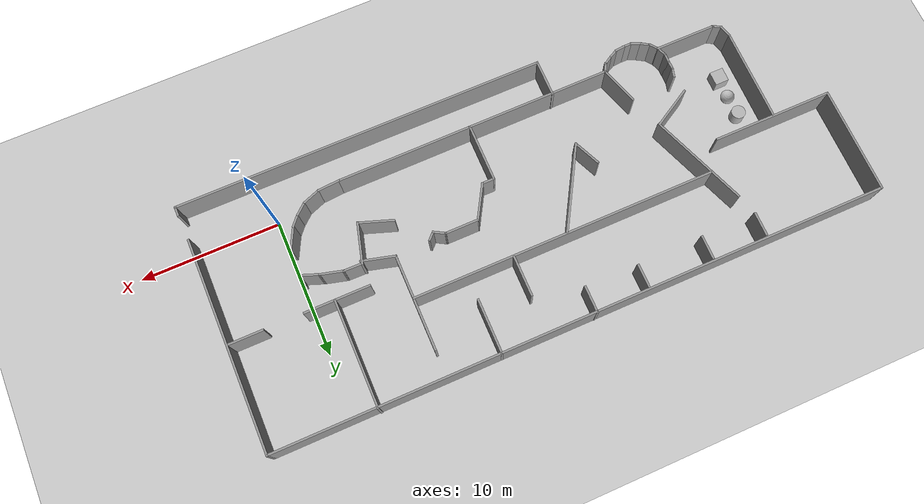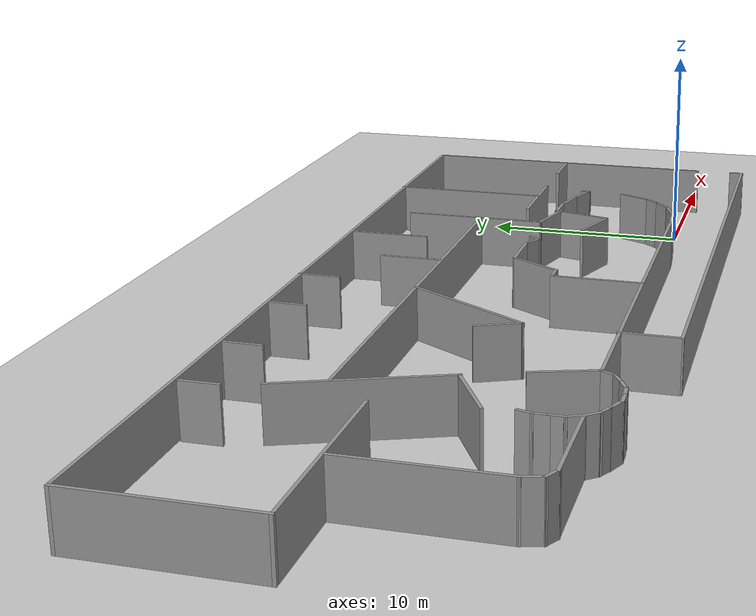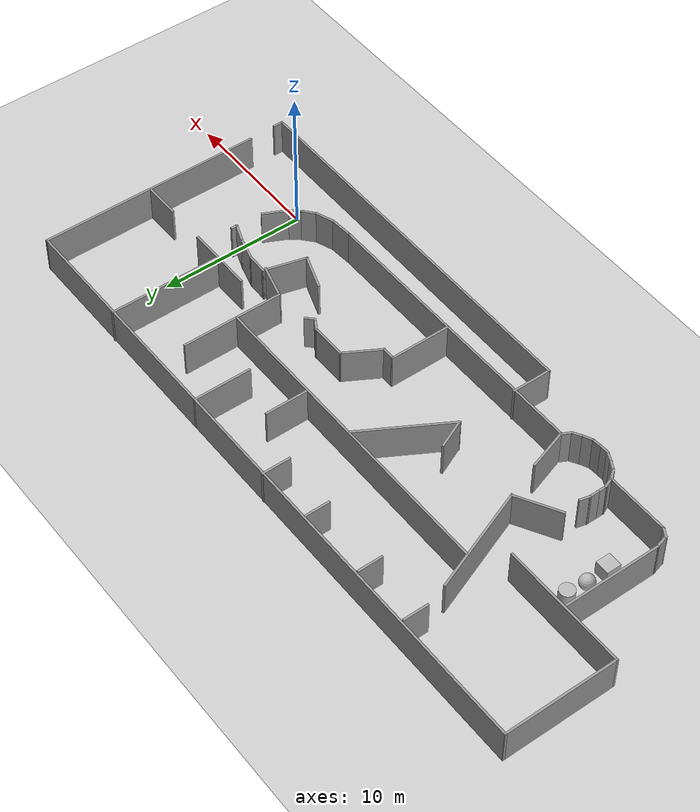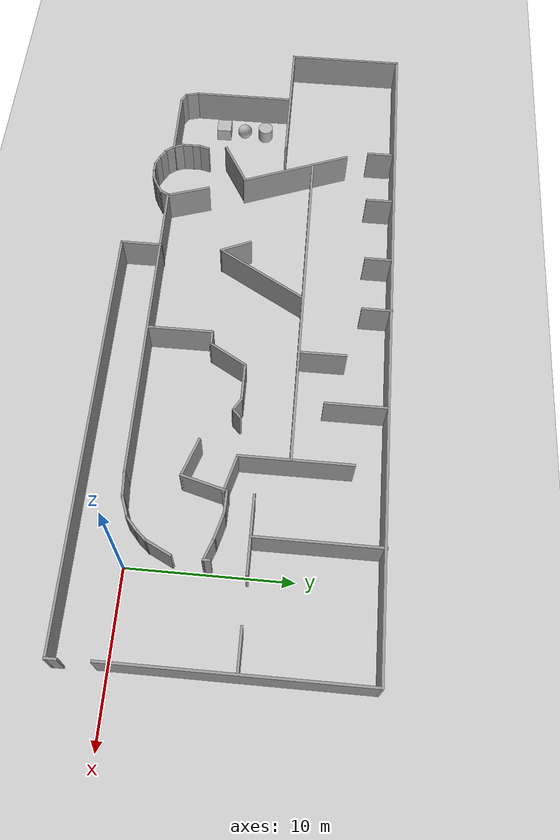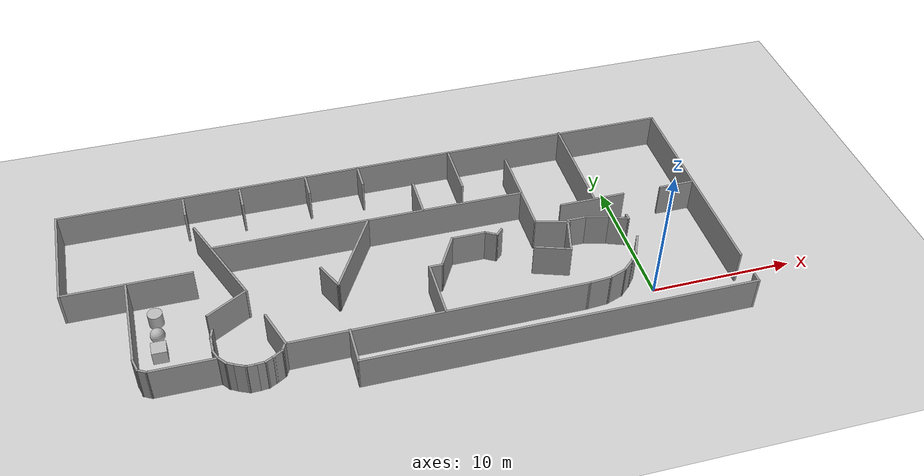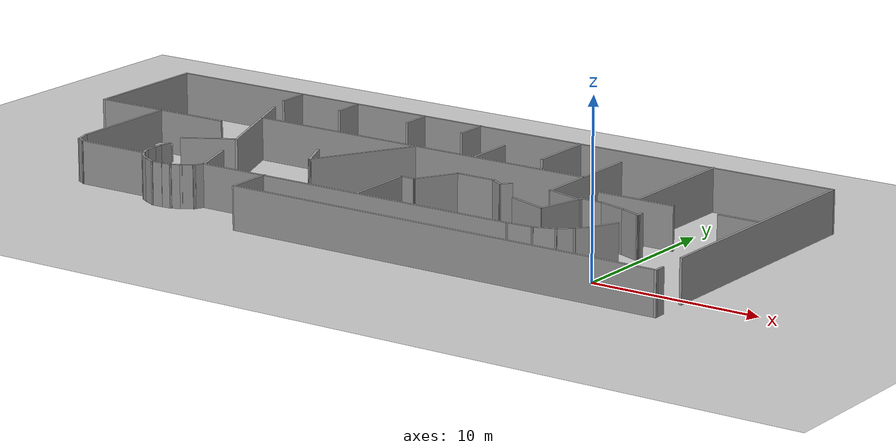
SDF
<sdf version="1.7">
 <world name="default">
  <light name="sun" type="directional">
   <pose>0 0 10 0 -0 0</pose>
   <diffuse>0.8 0.8 0.8 1</diffuse>
   <specular>0.2 0.2 0.2 1</specular>
   <attenuation>
    <range>1000</range>
    <constant>0.9</constant>
    <linear>0.01</linear>
    <quadratic>0.001</quadratic>
   </attenuation>
   <direction>-0.5 0.1 -0.9</direction>
   <spot><inner_angle>0</inner_angle><outer_angle>0</outer_angle><falloff>0</falloff></spot>
  </light>
  <model name="ground_plane">
   <static>1</static>
   <link name="link">
    <collision name="collision">
     <geometry><plane><normal>0 0 1</normal><size>100 100</size></plane></geometry>
     <surface>
      <contact><collide_bitmask>65535</collide_bitmask></contact>
      <friction><ode><mu>100</mu><mu2>50</mu2></ode></friction>
     </surface>
    </collision>
    <visual name="visual">
     <cast_shadows>0</cast_shadows>
     <geometry><plane><normal>0 0 1</normal><size>100 100</size></plane></geometry>
     <material>
      <script><uri>file://media/materials/scripts/gazebo.material</uri><name>Gazebo/Grey</name></script>
     </material>
    </visual>
   </link>
  </model>
  <gravity>0 0 -9.8</gravity>
  <magnetic_field>6e-06 2.3e-05 -4.2e-05</magnetic_field>
  <atmosphere type="adiabatic"/>
  <physics type="ode">
   <max_step_size>0.001</max_step_size>
   <real_time_factor>1</real_time_factor>
   <real_time_update_rate>1000</real_time_update_rate>
  </physics>
  <scene><ambient>0.4 0.4 0.4 1</ambient><background>0.7 0.7 0.7 1</background><shadows>1</shadows></scene>
  <spherical_coordinates>
   <surface_model>EARTH_WGS84</surface_model>
   <latitude_deg>0</latitude_deg>
   <longitude_deg>0</longitude_deg>
   <elevation>0</elevation>
   <heading_deg>0</heading_deg>
  </spherical_coordinates>
  <model name="textured_shapes">
   <pose>-32.8558 4.0923 0.5 0 -0 0</pose>
   <link name="box">
    <pose>0 -1.5 0 0 -0 0</pose>
    <collision name="collision"><geometry><box><size>1 1 1</size></box></geometry></collision>
    <visual name="visual">
     <geometry><box><size>1 1 1</size></box></geometry>
     <material>
      <script>
       <uri>model://textured_shapes/materials/scripts</uri>
       <uri>model://textured_shapes/materials/textures</uri>
       <name>TexturedShape/Squares</name>
      </script>
     </material>
    </visual>
    <inertial>
     <inertia><ixx>1</ixx><ixy>0</ixy><ixz>0</ixz><iyy>1</iyy><iyz>0</iyz><izz>1</izz></inertia>
     <mass>1</mass>
    </inertial>
   </link>
   <link name="sphere">
    <collision name="collision"><geometry><sphere><radius>0.5</radius></sphere></geometry></collision>
    <visual name="visual">
     <geometry><sphere><radius>0.5</radius></sphere></geometry>
     <material>
      <script>
       <uri>model://textured_shapes/materials/scripts</uri>
       <uri>model://textured_shapes/materials/textures</uri>
       <name>TexturedShape/Squares</name>
      </script>
     </material>
    </visual>
    <inertial>
     <inertia><ixx>1</ixx><ixy>0</ixy><ixz>0</ixz><iyy>1</iyy><iyz>0</iyz><izz>1</izz></inertia>
     <mass>1</mass>
    </inertial>
   </link>
   <link name="cylinder">
    <pose>0 1.5 0 0 -0 0</pose>
    <collision name="collision">
     <geometry><cylinder><radius>0.5</radius><length>1</length></cylinder></geometry>
    </collision>
    <visual name="visual">
     <geometry><cylinder><radius>0.5</radius><length>1</length></cylinder></geometry>
     <material>
      <script>
       <uri>model://textured_shapes/materials/scripts</uri>
       <uri>model://textured_shapes/materials/textures</uri>
       <name>TexturedShape/Squares</name>
      </script>
     </material>
    </visual>
    <inertial>
     <inertia><ixx>1</ixx><ixy>0</ixy><ixz>0</ixz><iyy>1</iyy><iyz>0</iyz><izz>1</izz></inertia>
     <mass>1</mass>
    </inertial>
   </link>
  </model>
  <model name="museum">
   <link name="Wall_0">
    <pose>1.36174 -6.35995 0 0 -0 0.00322</pose>
    <visual name="Wall_0_Visual">
     <pose>0 0 1.25 0 -0 0</pose>
     <geometry><box><size>20.2416 0.15 2.5</size></box></geometry>
     <material>
      <script><uri>file://media/materials/scripts/gazebo.material</uri><name>Gazebo/Grey</name></script>
      <ambient>1 1 1 1</ambient>
      <shader type="pixel"/>
     </material>
     <meta><layer>0</layer></meta>
    </visual>
    <collision name="Wall_0_Collision">
     <pose>0 0 1.25 0 -0 0</pose>
     <geometry><box><size>20.2416 0.15 2.5</size></box></geometry>
     <surface>
      <friction>
       <ode><mu>1</mu><mu2>1</mu2><fdir1>0 0 0</fdir1><slip1>0</slip1><slip2>0</slip2></ode>
       <torsional>
        <coefficient>1</coefficient>
        <patch_radius>0</patch_radius>
        <surface_radius>0</surface_radius>
        <use_patch_radius>1</use_patch_radius>
        <ode><slip>0</slip></ode>
       </torsional>
      </friction>
      <bounce><restitution_coefficient>0</restitution_coefficient><threshold>1e+06</threshold></bounce>
      <contact>
       <collide_without_contact>0</collide_without_contact>
       <collide_without_contact_bitmask>1</collide_without_contact_bitmask>
       <collide_bitmask>1</collide_bitmask>
       <ode>
        <soft_cfm>0</soft_cfm>
        <soft_erp>0.2</soft_erp>
        <kp>1e+13</kp>
        <kd>1</kd>
        <max_vel>0.01</max_vel>
        <min_depth>0</min_depth>
       </ode>
       <bullet>
        <split_impulse>1</split_impulse>
        <split_impulse_penetration_threshold>-0.01</split_impulse_penetration_threshold>
        <soft_cfm>0</soft_cfm>
        <soft_erp>0.2</soft_erp>
        <kp>1e+13</kp>
        <kd>1</kd>
       </bullet>
      </contact>
     </surface>
    </collision>
   </link>
   <link name="Wall_1">
    <pose>12.1586 -6.274 0 0 -0 0.071226</pose>
    <visual name="Wall_1_Visual">
     <pose>0 0 1.25 0 -0 0</pose>
     <geometry><box><size>1.65613 0.15 2.5</size></box></geometry>
     <material>
      <script><uri>file://media/materials/scripts/gazebo.material</uri><name>Gazebo/Grey</name></script>
      <ambient>1 1 1 1</ambient>
      <shader type="pixel"/>
     </material>
     <meta><layer>0</layer></meta>
    </visual>
    <collision name="Wall_1_Collision">
     <pose>0 0 1.25 0 -0 0</pose>
     <geometry><box><size>1.65613 0.15 2.5</size></box></geometry>
     <surface>
      <friction>
       <ode><mu>1</mu><mu2>1</mu2><fdir1>0 0 0</fdir1><slip1>0</slip1><slip2>0</slip2></ode>
       <torsional>
        <coefficient>1</coefficient>
        <patch_radius>0</patch_radius>
        <surface_radius>0</surface_radius>
        <use_patch_radius>1</use_patch_radius>
        <ode><slip>0</slip></ode>
       </torsional>
      </friction>
      <bounce><restitution_coefficient>0</restitution_coefficient><threshold>1e+06</threshold></bounce>
      <contact>
       <collide_without_contact>0</collide_without_contact>
       <collide_without_contact_bitmask>1</collide_without_contact_bitmask>
       <collide_bitmask>1</collide_bitmask>
       <ode>
        <soft_cfm>0</soft_cfm>
        <soft_erp>0.2</soft_erp>
        <kp>1e+13</kp>
        <kd>1</kd>
        <max_vel>0.01</max_vel>
        <min_depth>0</min_depth>
       </ode>
       <bullet>
        <split_impulse>1</split_impulse>
        <split_impulse_penetration_threshold>-0.01</split_impulse_penetration_threshold>
        <soft_cfm>0</soft_cfm>
        <soft_erp>0.2</soft_erp>
        <kp>1e+13</kp>
        <kd>1</kd>
       </bullet>
      </contact>
     </surface>
    </collision>
   </link>
   <link name="Wall_10">
    <pose>4.99403 0.023754 0 0 -0 0</pose>
    <visual name="Wall_10_Visual">
     <pose>0 0 1.25 0 -0 0</pose>
     <geometry><box><size>2.5 0.15 2.5</size></box></geometry>
     <material>
      <script><uri>file://media/materials/scripts/gazebo.material</uri><name>Gazebo/Grey</name></script>
      <ambient>1 1 1 1</ambient>
      <shader type="pixel"/>
     </material>
     <meta><layer>0</layer></meta>
    </visual>
    <collision name="Wall_10_Collision">
     <pose>0 0 1.25 0 -0 0</pose>
     <geometry><box><size>2.5 0.15 2.5</size></box></geometry>
     <surface>
      <friction>
       <ode><mu>1</mu><mu2>1</mu2><fdir1>0 0 0</fdir1><slip1>0</slip1><slip2>0</slip2></ode>
       <torsional>
        <coefficient>1</coefficient>
        <patch_radius>0</patch_radius>
        <surface_radius>0</surface_radius>
        <use_patch_radius>1</use_patch_radius>
        <ode><slip>0</slip></ode>
       </torsional>
      </friction>
      <bounce><restitution_coefficient>0</restitution_coefficient><threshold>1e+06</threshold></bounce>
      <contact>
       <collide_without_contact>0</collide_without_contact>
       <collide_without_contact_bitmask>1</collide_without_contact_bitmask>
       <collide_bitmask>1</collide_bitmask>
       <ode>
        <soft_cfm>0</soft_cfm>
        <soft_erp>0.2</soft_erp>
        <kp>1e+13</kp>
        <kd>1</kd>
        <max_vel>0.01</max_vel>
        <min_depth>0</min_depth>
       </ode>
       <bullet>
        <split_impulse>1</split_impulse>
        <split_impulse_penetration_threshold>-0.01</split_impulse_penetration_threshold>
        <soft_cfm>0</soft_cfm>
        <soft_erp>0.2</soft_erp>
        <kp>1e+13</kp>
        <kd>1</kd>
       </bullet>
      </contact>
     </surface>
    </collision>
   </link>
   <link name="Wall_11">
    <pose>6.53709 -0.188746 0 0 0 -0.523599</pose>
    <visual name="Wall_11_Visual">
     <pose>0 0 1.25 0 -0 0</pose>
     <geometry><box><size>1 0.15 2.5</size></box></geometry>
     <material>
      <script><uri>file://media/materials/scripts/gazebo.material</uri><name>Gazebo/Grey</name></script>
      <ambient>1 1 1 1</ambient>
      <shader type="pixel"/>
     </material>
     <meta><layer>0</layer></meta>
    </visual>
    <collision name="Wall_11_Collision">
     <pose>0 0 1.25 0 -0 0</pose>
     <geometry><box><size>1 0.15 2.5</size></box></geometry>
     <surface>
      <friction>
       <ode><mu>1</mu><mu2>1</mu2><fdir1>0 0 0</fdir1><slip1>0</slip1><slip2>0</slip2></ode>
       <torsional>
        <coefficient>1</coefficient>
        <patch_radius>0</patch_radius>
        <surface_radius>0</surface_radius>
        <use_patch_radius>1</use_patch_radius>
        <ode><slip>0</slip></ode>
       </torsional>
      </friction>
      <bounce><restitution_coefficient>0</restitution_coefficient><threshold>1e+06</threshold></bounce>
      <contact>
       <collide_without_contact>0</collide_without_contact>
       <collide_without_contact_bitmask>1</collide_without_contact_bitmask>
       <collide_bitmask>1</collide_bitmask>
       <ode>
        <soft_cfm>0</soft_cfm>
        <soft_erp>0.2</soft_erp>
        <kp>1e+13</kp>
        <kd>1</kd>
        <max_vel>0.01</max_vel>
        <min_depth>0</min_depth>
       </ode>
       <bullet>
        <split_impulse>1</split_impulse>
        <split_impulse_penetration_threshold>-0.01</split_impulse_penetration_threshold>
        <soft_cfm>0</soft_cfm>
        <soft_erp>0.2</soft_erp>
        <kp>1e+13</kp>
        <kd>1</kd>
       </bullet>
      </contact>
     </surface>
    </collision>
   </link>
   <link name="Wall_12">
    <pose>7.11728 -0.189114 0 0 -0 0.785398</pose>
    <visual name="Wall_12_Visual">
     <pose>0 0 1.25 0 -0 0</pose>
     <geometry><box><size>0.75 0.15 2.5</size></box></geometry>
     <material>
      <script><uri>file://media/materials/scripts/gazebo.material</uri><name>Gazebo/Grey</name></script>
      <ambient>1 1 1 1</ambient>
      <shader type="pixel"/>
     </material>
     <meta><layer>0</layer></meta>
    </visual>
    <collision name="Wall_12_Collision">
     <pose>0 0 1.25 0 -0 0</pose>
     <geometry><box><size>0.75 0.15 2.5</size></box></geometry>
     <surface>
      <friction>
       <ode><mu>1</mu><mu2>1</mu2><fdir1>0 0 0</fdir1><slip1>0</slip1><slip2>0</slip2></ode>
       <torsional>
        <coefficient>1</coefficient>
        <patch_radius>0</patch_radius>
        <surface_radius>0</surface_radius>
        <use_patch_radius>1</use_patch_radius>
        <ode><slip>0</slip></ode>
       </torsional>
      </friction>
      <bounce><restitution_coefficient>0</restitution_coefficient><threshold>1e+06</threshold></bounce>
      <contact>
       <collide_without_contact>0</collide_without_contact>
       <collide_without_contact_bitmask>1</collide_without_contact_bitmask>
       <collide_bitmask>1</collide_bitmask>
       <ode>
        <soft_cfm>0</soft_cfm>
        <soft_erp>0.2</soft_erp>
        <kp>1e+13</kp>
        <kd>1</kd>
        <max_vel>0.01</max_vel>
        <min_depth>0</min_depth>
       </ode>
       <bullet>
        <split_impulse>1</split_impulse>
        <split_impulse_penetration_threshold>-0.01</split_impulse_penetration_threshold>
        <soft_cfm>0</soft_cfm>
        <soft_erp>0.2</soft_erp>
        <kp>1e+13</kp>
        <kd>1</kd>
       </bullet>
      </contact>
     </surface>
    </collision>
   </link>
   <link name="Wall_14">
    <pose>10.1587 -2.61733 0 0 0 -0.33835</pose>
    <visual name="Wall_14_Visual">
     <pose>0 0 1.25 0 -0 0</pose>
     <geometry><box><size>2.58802 0.15 2.5</size></box></geometry>
     <material>
      <script><uri>file://media/materials/scripts/gazebo.material</uri><name>Gazebo/Grey</name></script>
      <ambient>1 1 1 1</ambient>
      <shader type="pixel"/>
     </material>
     <meta><layer>0</layer></meta>
    </visual>
    <collision name="Wall_14_Collision">
     <pose>0 0 1.25 0 -0 0</pose>
     <geometry><box><size>2.58802 0.15 2.5</size></box></geometry>
     <surface>
      <friction>
       <ode><mu>1</mu><mu2>1</mu2><fdir1>0 0 0</fdir1><slip1>0</slip1><slip2>0</slip2></ode>
       <torsional>
        <coefficient>1</coefficient>
        <patch_radius>0</patch_radius>
        <surface_radius>0</surface_radius>
        <use_patch_radius>1</use_patch_radius>
        <ode><slip>0</slip></ode>
       </torsional>
      </friction>
      <bounce><restitution_coefficient>0</restitution_coefficient><threshold>1e+06</threshold></bounce>
      <contact>
       <collide_without_contact>0</collide_without_contact>
       <collide_without_contact_bitmask>1</collide_without_contact_bitmask>
       <collide_bitmask>1</collide_bitmask>
       <ode>
        <soft_cfm>0</soft_cfm>
        <soft_erp>0.2</soft_erp>
        <kp>1e+13</kp>
        <kd>1</kd>
        <max_vel>0.01</max_vel>
        <min_depth>0</min_depth>
       </ode>
       <bullet>
        <split_impulse>1</split_impulse>
        <split_impulse_penetration_threshold>-0.01</split_impulse_penetration_threshold>
        <soft_cfm>0</soft_cfm>
        <soft_erp>0.2</soft_erp>
        <kp>1e+13</kp>
        <kd>1</kd>
       </bullet>
      </contact>
     </surface>
    </collision>
   </link>
   <link name="Wall_15">
    <pose>11.6877 -1.62545 0 0 -0 1.309</pose>
    <visual name="Wall_15_Visual">
     <pose>0 0 1.25 0 -0 0</pose>
     <geometry><box><size>3 0.15 2.5</size></box></geometry>
     <material>
      <script><uri>file://media/materials/scripts/gazebo.material</uri><name>Gazebo/Grey</name></script>
      <ambient>1 1 1 1</ambient>
      <shader type="pixel"/>
     </material>
     <meta><layer>0</layer></meta>
    </visual>
    <collision name="Wall_15_Collision">
     <pose>0 0 1.25 0 -0 0</pose>
     <geometry><box><size>3 0.15 2.5</size></box></geometry>
     <surface>
      <friction>
       <ode><mu>1</mu><mu2>1</mu2><fdir1>0 0 0</fdir1><slip1>0</slip1><slip2>0</slip2></ode>
       <torsional>
        <coefficient>1</coefficient>
        <patch_radius>0</patch_radius>
        <surface_radius>0</surface_radius>
        <use_patch_radius>1</use_patch_radius>
        <ode><slip>0</slip></ode>
       </torsional>
      </friction>
      <bounce><restitution_coefficient>0</restitution_coefficient><threshold>1e+06</threshold></bounce>
      <contact>
       <collide_without_contact>0</collide_without_contact>
       <collide_without_contact_bitmask>1</collide_without_contact_bitmask>
       <collide_bitmask>1</collide_bitmask>
       <ode>
        <soft_cfm>0</soft_cfm>
        <soft_erp>0.2</soft_erp>
        <kp>1e+13</kp>
        <kd>1</kd>
        <max_vel>0.01</max_vel>
        <min_depth>0</min_depth>
       </ode>
       <bullet>
        <split_impulse>1</split_impulse>
        <split_impulse_penetration_threshold>-0.01</split_impulse_penetration_threshold>
        <soft_cfm>0</soft_cfm>
        <soft_erp>0.2</soft_erp>
        <kp>1e+13</kp>
        <kd>1</kd>
       </bullet>
      </contact>
     </surface>
    </collision>
   </link>
   <link name="Wall_16">
    <pose>12.7085 -0.282917 0 0 0 -0.020832</pose>
    <visual name="Wall_16_Visual">
     <pose>0 0 1.25 0 -0 0</pose>
     <geometry><box><size>1.4744 0.15 2.5</size></box></geometry>
     <material>
      <script><uri>file://media/materials/scripts/gazebo.material</uri><name>Gazebo/Grey</name></script>
      <ambient>1 1 1 1</ambient>
      <shader type="pixel"/>
     </material>
     <meta><layer>0</layer></meta>
    </visual>
    <collision name="Wall_16_Collision">
     <pose>0 0 1.25 0 -0 0</pose>
     <geometry><box><size>1.4744 0.15 2.5</size></box></geometry>
     <surface>
      <friction>
       <ode><mu>1</mu><mu2>1</mu2><fdir1>0 0 0</fdir1><slip1>0</slip1><slip2>0</slip2></ode>
       <torsional>
        <coefficient>1</coefficient>
        <patch_radius>0</patch_radius>
        <surface_radius>0</surface_radius>
        <use_patch_radius>1</use_patch_radius>
        <ode><slip>0</slip></ode>
       </torsional>
      </friction>
      <bounce><restitution_coefficient>0</restitution_coefficient><threshold>1e+06</threshold></bounce>
      <contact>
       <collide_without_contact>0</collide_without_contact>
       <collide_without_contact_bitmask>1</collide_without_contact_bitmask>
       <collide_bitmask>1</collide_bitmask>
       <ode>
        <soft_cfm>0</soft_cfm>
        <soft_erp>0.2</soft_erp>
        <kp>1e+13</kp>
        <kd>1</kd>
        <max_vel>0.01</max_vel>
        <min_depth>0</min_depth>
       </ode>
       <bullet>
        <split_impulse>1</split_impulse>
        <split_impulse_penetration_threshold>-0.01</split_impulse_penetration_threshold>
        <soft_cfm>0</soft_cfm>
        <soft_erp>0.2</soft_erp>
        <kp>1e+13</kp>
        <kd>1</kd>
       </bullet>
      </contact>
     </surface>
    </collision>
   </link>
   <link name="Wall_17">
    <pose>14.1433 -0.503766 0 0 0 -0.261799</pose>
    <visual name="Wall_17_Visual">
     <pose>0 0 1.25 0 -0 0</pose>
     <geometry><box><size>1.75 0.15 2.5</size></box></geometry>
     <material>
      <script><uri>file://media/materials/scripts/gazebo.material</uri><name>Gazebo/Grey</name></script>
      <ambient>1 1 1 1</ambient>
      <shader type="pixel"/>
     </material>
     <meta><layer>0</layer></meta>
    </visual>
    <collision name="Wall_17_Collision">
     <pose>0 0 1.25 0 -0 0</pose>
     <geometry><box><size>1.75 0.15 2.5</size></box></geometry>
     <surface>
      <friction>
       <ode><mu>1</mu><mu2>1</mu2><fdir1>0 0 0</fdir1><slip1>0</slip1><slip2>0</slip2></ode>
       <torsional>
        <coefficient>1</coefficient>
        <patch_radius>0</patch_radius>
        <surface_radius>0</surface_radius>
        <use_patch_radius>1</use_patch_radius>
        <ode><slip>0</slip></ode>
       </torsional>
      </friction>
      <bounce><restitution_coefficient>0</restitution_coefficient><threshold>1e+06</threshold></bounce>
      <contact>
       <collide_without_contact>0</collide_without_contact>
       <collide_without_contact_bitmask>1</collide_without_contact_bitmask>
       <collide_bitmask>1</collide_bitmask>
       <ode>
        <soft_cfm>0</soft_cfm>
        <soft_erp>0.2</soft_erp>
        <kp>1e+13</kp>
        <kd>1</kd>
        <max_vel>0.01</max_vel>
        <min_depth>0</min_depth>
       </ode>
       <bullet>
        <split_impulse>1</split_impulse>
        <split_impulse_penetration_threshold>-0.01</split_impulse_penetration_threshold>
        <soft_cfm>0</soft_cfm>
        <soft_erp>0.2</soft_erp>
        <kp>1e+13</kp>
        <kd>1</kd>
       </bullet>
      </contact>
     </surface>
    </collision>
   </link>
   <link name="Wall_18">
    <pose>15.5429 -0.945865 0 0 0 -0.358731</pose>
    <visual name="Wall_18_Visual">
     <pose>0 0 1.25 0 -0 0</pose>
     <geometry><box><size>1.48895 0.15 2.5</size></box></geometry>
     <material>
      <script><uri>file://media/materials/scripts/gazebo.material</uri><name>Gazebo/Grey</name></script>
      <ambient>1 1 1 1</ambient>
      <shader type="pixel"/>
     </material>
     <meta><layer>0</layer></meta>
    </visual>
    <collision name="Wall_18_Collision">
     <pose>0 0 1.25 0 -0 0</pose>
     <geometry><box><size>1.48895 0.15 2.5</size></box></geometry>
     <surface>
      <friction>
       <ode><mu>1</mu><mu2>1</mu2><fdir1>0 0 0</fdir1><slip1>0</slip1><slip2>0</slip2></ode>
       <torsional>
        <coefficient>1</coefficient>
        <patch_radius>0</patch_radius>
        <surface_radius>0</surface_radius>
        <use_patch_radius>1</use_patch_radius>
        <ode><slip>0</slip></ode>
       </torsional>
      </friction>
      <bounce><restitution_coefficient>0</restitution_coefficient><threshold>1e+06</threshold></bounce>
      <contact>
       <collide_without_contact>0</collide_without_contact>
       <collide_without_contact_bitmask>1</collide_without_contact_bitmask>
       <collide_bitmask>1</collide_bitmask>
       <ode>
        <soft_cfm>0</soft_cfm>
        <soft_erp>0.2</soft_erp>
        <kp>1e+13</kp>
        <kd>1</kd>
        <max_vel>0.01</max_vel>
        <min_depth>0</min_depth>
       </ode>
       <bullet>
        <split_impulse>1</split_impulse>
        <split_impulse_penetration_threshold>-0.01</split_impulse_penetration_threshold>
        <soft_cfm>0</soft_cfm>
        <soft_erp>0.2</soft_erp>
        <kp>1e+13</kp>
        <kd>1</kd>
       </bullet>
      </contact>
     </surface>
    </collision>
   </link>
   <link name="Wall_19">
    <pose>16.1697 -1.00591 0 0 -0 1.5708</pose>
    <visual name="Wall_19_Visual">
     <pose>0 0 1.25 0 -0 0</pose>
     <geometry><box><size>0.5 0.15 2.5</size></box></geometry>
     <material>
      <script><uri>file://media/materials/scripts/gazebo.material</uri><name>Gazebo/Grey</name></script>
      <ambient>1 1 1 1</ambient>
      <shader type="pixel"/>
     </material>
     <meta><layer>0</layer></meta>
    </visual>
    <collision name="Wall_19_Collision">
     <pose>0 0 1.25 0 -0 0</pose>
     <geometry><box><size>0.5 0.15 2.5</size></box></geometry>
     <surface>
      <friction>
       <ode><mu>1</mu><mu2>1</mu2><fdir1>0 0 0</fdir1><slip1>0</slip1><slip2>0</slip2></ode>
       <torsional>
        <coefficient>1</coefficient>
        <patch_radius>0</patch_radius>
        <surface_radius>0</surface_radius>
        <use_patch_radius>1</use_patch_radius>
        <ode><slip>0</slip></ode>
       </torsional>
      </friction>
      <bounce><restitution_coefficient>0</restitution_coefficient><threshold>1e+06</threshold></bounce>
      <contact>
       <collide_without_contact>0</collide_without_contact>
       <collide_without_contact_bitmask>1</collide_without_contact_bitmask>
       <collide_bitmask>1</collide_bitmask>
       <ode>
        <soft_cfm>0</soft_cfm>
        <soft_erp>0.2</soft_erp>
        <kp>1e+13</kp>
        <kd>1</kd>
        <max_vel>0.01</max_vel>
        <min_depth>0</min_depth>
       </ode>
       <bullet>
        <split_impulse>1</split_impulse>
        <split_impulse_penetration_threshold>-0.01</split_impulse_penetration_threshold>
        <soft_cfm>0</soft_cfm>
        <soft_erp>0.2</soft_erp>
        <kp>1e+13</kp>
        <kd>1</kd>
       </bullet>
      </contact>
     </surface>
    </collision>
   </link>
   <link name="Wall_2">
    <pose>13.4937 -6.00412 0 0 -0 0.354727</pose>
    <visual name="Wall_2_Visual">
     <pose>0 0 1.25 0 -0 0</pose>
     <geometry><box><size>1.39543 0.15 2.5</size></box></geometry>
     <material>
      <script><uri>file://media/materials/scripts/gazebo.material</uri><name>Gazebo/Grey</name></script>
      <ambient>1 1 1 1</ambient>
      <shader type="pixel"/>
     </material>
     <meta><layer>0</layer></meta>
    </visual>
    <collision name="Wall_2_Collision">
     <pose>0 0 1.25 0 -0 0</pose>
     <geometry><box><size>1.39543 0.15 2.5</size></box></geometry>
     <surface>
      <friction>
       <ode><mu>1</mu><mu2>1</mu2><fdir1>0 0 0</fdir1><slip1>0</slip1><slip2>0</slip2></ode>
       <torsional>
        <coefficient>1</coefficient>
        <patch_radius>0</patch_radius>
        <surface_radius>0</surface_radius>
        <use_patch_radius>1</use_patch_radius>
        <ode><slip>0</slip></ode>
       </torsional>
      </friction>
      <bounce><restitution_coefficient>0</restitution_coefficient><threshold>1e+06</threshold></bounce>
      <contact>
       <collide_without_contact>0</collide_without_contact>
       <collide_without_contact_bitmask>1</collide_without_contact_bitmask>
       <collide_bitmask>1</collide_bitmask>
       <ode>
        <soft_cfm>0</soft_cfm>
        <soft_erp>0.2</soft_erp>
        <kp>1e+13</kp>
        <kd>1</kd>
        <max_vel>0.01</max_vel>
        <min_depth>0</min_depth>
       </ode>
       <bullet>
        <split_impulse>1</split_impulse>
        <split_impulse_penetration_threshold>-0.01</split_impulse_penetration_threshold>
        <soft_cfm>0</soft_cfm>
        <soft_erp>0.2</soft_erp>
        <kp>1e+13</kp>
        <kd>1</kd>
       </bullet>
      </contact>
     </surface>
    </collision>
   </link>
   <link name="Wall_21">
    <pose>14.4565 1.31728 0 0 -0 0</pose>
    <visual name="Wall_21_Visual">
     <pose>0 0 1.25 0 -0 0</pose>
     <geometry><box><size>4.75 0.15 2.5</size></box></geometry>
     <material>
      <script><uri>file://media/materials/scripts/gazebo.material</uri><name>Gazebo/Grey</name></script>
      <ambient>1 1 1 1</ambient>
      <shader type="pixel"/>
     </material>
     <meta><layer>0</layer></meta>
    </visual>
    <collision name="Wall_21_Collision">
     <pose>0 0 1.25 0 -0 0</pose>
     <geometry><box><size>4.75 0.15 2.5</size></box></geometry>
     <surface>
      <friction>
       <ode><mu>1</mu><mu2>1</mu2><fdir1>0 0 0</fdir1><slip1>0</slip1><slip2>0</slip2></ode>
       <torsional>
        <coefficient>1</coefficient>
        <patch_radius>0</patch_radius>
        <surface_radius>0</surface_radius>
        <use_patch_radius>1</use_patch_radius>
        <ode><slip>0</slip></ode>
       </torsional>
      </friction>
      <bounce><restitution_coefficient>0</restitution_coefficient><threshold>1e+06</threshold></bounce>
      <contact>
       <collide_without_contact>0</collide_without_contact>
       <collide_without_contact_bitmask>1</collide_without_contact_bitmask>
       <collide_bitmask>1</collide_bitmask>
       <ode>
        <soft_cfm>0</soft_cfm>
        <soft_erp>0.2</soft_erp>
        <kp>1e+13</kp>
        <kd>1</kd>
        <max_vel>0.01</max_vel>
        <min_depth>0</min_depth>
       </ode>
       <bullet>
        <split_impulse>1</split_impulse>
        <split_impulse_penetration_threshold>-0.01</split_impulse_penetration_threshold>
        <soft_cfm>0</soft_cfm>
        <soft_erp>0.2</soft_erp>
        <kp>1e+13</kp>
        <kd>1</kd>
       </bullet>
      </contact>
     </surface>
    </collision>
   </link>
   <link name="Wall_23">
    <pose>20.8037 1.29717 0 0 -0 0</pose>
    <visual name="Wall_23_Visual">
     <pose>0 0 1.25 0 -0 0</pose>
     <geometry><box><size>2.5 0.15 2.5</size></box></geometry>
     <material>
      <script><uri>file://media/materials/scripts/gazebo.material</uri><name>Gazebo/Grey</name></script>
      <ambient>1 1 1 1</ambient>
      <shader type="pixel"/>
     </material>
     <meta><layer>0</layer></meta>
    </visual>
    <collision name="Wall_23_Collision">
     <pose>0 0 1.25 0 -0 0</pose>
     <geometry><box><size>2.5 0.15 2.5</size></box></geometry>
     <surface>
      <friction>
       <ode><mu>1</mu><mu2>1</mu2><fdir1>0 0 0</fdir1><slip1>0</slip1><slip2>0</slip2></ode>
       <torsional>
        <coefficient>1</coefficient>
        <patch_radius>0</patch_radius>
        <surface_radius>0</surface_radius>
        <use_patch_radius>1</use_patch_radius>
        <ode><slip>0</slip></ode>
       </torsional>
      </friction>
      <bounce><restitution_coefficient>0</restitution_coefficient><threshold>1e+06</threshold></bounce>
      <contact>
       <collide_without_contact>0</collide_without_contact>
       <collide_without_contact_bitmask>1</collide_without_contact_bitmask>
       <collide_bitmask>1</collide_bitmask>
       <ode>
        <soft_cfm>0</soft_cfm>
        <soft_erp>0.2</soft_erp>
        <kp>1e+13</kp>
        <kd>1</kd>
        <max_vel>0.01</max_vel>
        <min_depth>0</min_depth>
       </ode>
       <bullet>
        <split_impulse>1</split_impulse>
        <split_impulse_penetration_threshold>-0.01</split_impulse_penetration_threshold>
        <soft_cfm>0</soft_cfm>
        <soft_erp>0.2</soft_erp>
        <kp>1e+13</kp>
        <kd>1</kd>
       </bullet>
      </contact>
     </surface>
    </collision>
   </link>
   <link name="Wall_25">
    <pose>9.82211 3.56475 0 0 0 -1.5708</pose>
    <visual name="Wall_25_Visual">
     <pose>0 0 1.25 0 -0 0</pose>
     <geometry><box><size>7 0.15 2.5</size></box></geometry>
     <material>
      <script><uri>file://media/materials/scripts/gazebo.material</uri><name>Gazebo/Grey</name></script>
      <ambient>1 1 1 1</ambient>
      <shader type="pixel"/>
     </material>
     <meta><layer>0</layer></meta>
    </visual>
    <collision name="Wall_25_Collision">
     <pose>0 0 1.25 0 -0 0</pose>
     <geometry><box><size>7 0.15 2.5</size></box></geometry>
     <surface>
      <friction>
       <ode><mu>1</mu><mu2>1</mu2><fdir1>0 0 0</fdir1><slip1>0</slip1><slip2>0</slip2></ode>
       <torsional>
        <coefficient>1</coefficient>
        <patch_radius>0</patch_radius>
        <surface_radius>0</surface_radius>
        <use_patch_radius>1</use_patch_radius>
        <ode><slip>0</slip></ode>
       </torsional>
      </friction>
      <bounce><restitution_coefficient>0</restitution_coefficient><threshold>1e+06</threshold></bounce>
      <contact>
       <collide_without_contact>0</collide_without_contact>
       <collide_without_contact_bitmask>1</collide_without_contact_bitmask>
       <collide_bitmask>1</collide_bitmask>
       <ode>
        <soft_cfm>0</soft_cfm>
        <soft_erp>0.2</soft_erp>
        <kp>1e+13</kp>
        <kd>1</kd>
        <max_vel>0.01</max_vel>
        <min_depth>0</min_depth>
       </ode>
       <bullet>
        <split_impulse>1</split_impulse>
        <split_impulse_penetration_threshold>-0.01</split_impulse_penetration_threshold>
        <soft_cfm>0</soft_cfm>
        <soft_erp>0.2</soft_erp>
        <kp>1e+13</kp>
        <kd>1</kd>
       </bullet>
      </contact>
     </surface>
    </collision>
   </link>
   <link name="Wall_26">
    <pose>10.9571 -0.164361 0 0 0 -0.261799</pose>
    <visual name="Wall_26_Visual">
     <pose>0 0 1.25 0 -0 0</pose>
     <geometry><box><size>2.5 0.15 2.5</size></box></geometry>
     <material>
      <script><uri>file://media/materials/scripts/gazebo.material</uri><name>Gazebo/Grey</name></script>
      <ambient>1 1 1 1</ambient>
      <shader type="pixel"/>
     </material>
     <meta><layer>0</layer></meta>
    </visual>
    <collision name="Wall_26_Collision">
     <pose>0 0 1.25 0 -0 0</pose>
     <geometry><box><size>2.5 0.15 2.5</size></box></geometry>
     <surface>
      <friction>
       <ode><mu>1</mu><mu2>1</mu2><fdir1>0 0 0</fdir1><slip1>0</slip1><slip2>0</slip2></ode>
       <torsional>
        <coefficient>1</coefficient>
        <patch_radius>0</patch_radius>
        <surface_radius>0</surface_radius>
        <use_patch_radius>1</use_patch_radius>
        <ode><slip>0</slip></ode>
       </torsional>
      </friction>
      <bounce><restitution_coefficient>0</restitution_coefficient><threshold>1e+06</threshold></bounce>
      <contact>
       <collide_without_contact>0</collide_without_contact>
       <collide_without_contact_bitmask>1</collide_without_contact_bitmask>
       <collide_bitmask>1</collide_bitmask>
       <ode>
        <soft_cfm>0</soft_cfm>
        <soft_erp>0.2</soft_erp>
        <kp>1e+13</kp>
        <kd>1</kd>
        <max_vel>0.01</max_vel>
        <min_depth>0</min_depth>
       </ode>
       <bullet>
        <split_impulse>1</split_impulse>
        <split_impulse_penetration_threshold>-0.01</split_impulse_penetration_threshold>
        <soft_cfm>0</soft_cfm>
        <soft_erp>0.2</soft_erp>
        <kp>1e+13</kp>
        <kd>1</kd>
       </bullet>
      </contact>
     </surface>
    </collision>
   </link>
   <link name="Wall_28">
    <pose>-17.892 1.3048 0 0 -0 3.14159</pose>
    <visual name="Wall_28_Visual">
     <pose>0 0 1.25 0 -0 0</pose>
     <geometry><box><size>8.75 0.15 2.5</size></box></geometry>
     <material>
      <script><uri>file://media/materials/scripts/gazebo.material</uri><name>Gazebo/Grey</name></script>
      <ambient>1 1 1 1</ambient>
      <shader type="pixel"/>
     </material>
     <meta><layer>0</layer></meta>
    </visual>
    <collision name="Wall_28_Collision">
     <pose>0 0 1.25 0 -0 0</pose>
     <geometry><box><size>8.75 0.15 2.5</size></box></geometry>
     <surface>
      <friction>
       <ode><mu>1</mu><mu2>1</mu2><fdir1>0 0 0</fdir1><slip1>0</slip1><slip2>0</slip2></ode>
       <torsional>
        <coefficient>1</coefficient>
        <patch_radius>0</patch_radius>
        <surface_radius>0</surface_radius>
        <use_patch_radius>1</use_patch_radius>
        <ode><slip>0</slip></ode>
       </torsional>
      </friction>
      <bounce><restitution_coefficient>0</restitution_coefficient><threshold>1e+06</threshold></bounce>
      <contact>
       <collide_without_contact>0</collide_without_contact>
       <collide_without_contact_bitmask>1</collide_without_contact_bitmask>
       <collide_bitmask>1</collide_bitmask>
       <ode>
        <soft_cfm>0</soft_cfm>
        <soft_erp>0.2</soft_erp>
        <kp>1e+13</kp>
        <kd>1</kd>
        <max_vel>0.01</max_vel>
        <min_depth>0</min_depth>
       </ode>
       <bullet>
        <split_impulse>1</split_impulse>
        <split_impulse_penetration_threshold>-0.01</split_impulse_penetration_threshold>
        <soft_cfm>0</soft_cfm>
        <soft_erp>0.2</soft_erp>
        <kp>1e+13</kp>
        <kd>1</kd>
       </bullet>
      </contact>
     </surface>
    </collision>
   </link>
   <link name="Wall_29">
    <pose>-22.192 5.1048 0 0 -0 1.5708</pose>
    <visual name="Wall_29_Visual">
     <pose>0 0 1.25 0 -0 0</pose>
     <geometry><box><size>7.75 0.15 2.5</size></box></geometry>
     <material>
      <script><uri>file://media/materials/scripts/gazebo.material</uri><name>Gazebo/Grey</name></script>
      <ambient>1 1 1 1</ambient>
      <shader type="pixel"/>
     </material>
     <meta><layer>0</layer></meta>
    </visual>
    <collision name="Wall_29_Collision">
     <pose>0 0 1.25 0 -0 0</pose>
     <geometry><box><size>7.75 0.15 2.5</size></box></geometry>
     <surface>
      <friction>
       <ode><mu>1</mu><mu2>1</mu2><fdir1>0 0 0</fdir1><slip1>0</slip1><slip2>0</slip2></ode>
       <torsional>
        <coefficient>1</coefficient>
        <patch_radius>0</patch_radius>
        <surface_radius>0</surface_radius>
        <use_patch_radius>1</use_patch_radius>
        <ode><slip>0</slip></ode>
       </torsional>
      </friction>
      <bounce><restitution_coefficient>0</restitution_coefficient><threshold>1e+06</threshold></bounce>
      <contact>
       <collide_without_contact>0</collide_without_contact>
       <collide_without_contact_bitmask>1</collide_without_contact_bitmask>
       <collide_bitmask>1</collide_bitmask>
       <ode>
        <soft_cfm>0</soft_cfm>
        <soft_erp>0.2</soft_erp>
        <kp>1e+13</kp>
        <kd>1</kd>
        <max_vel>0.01</max_vel>
        <min_depth>0</min_depth>
       </ode>
       <bullet>
        <split_impulse>1</split_impulse>
        <split_impulse_penetration_threshold>-0.01</split_impulse_penetration_threshold>
        <soft_cfm>0</soft_cfm>
        <soft_erp>0.2</soft_erp>
        <kp>1e+13</kp>
        <kd>1</kd>
       </bullet>
      </contact>
     </surface>
    </collision>
   </link>
   <link name="Wall_3">
    <pose>14.44 -5.47676 0 0 -0 0.719878</pose>
    <visual name="Wall_3_Visual">
     <pose>0 0 1.25 0 -0 0</pose>
     <geometry><box><size>1.09363 0.15 2.5</size></box></geometry>
     <material>
      <script><uri>file://media/materials/scripts/gazebo.material</uri><name>Gazebo/Grey</name></script>
      <ambient>1 1 1 1</ambient>
      <shader type="pixel"/>
     </material>
     <meta><layer>0</layer></meta>
    </visual>
    <collision name="Wall_3_Collision">
     <pose>0 0 1.25 0 -0 0</pose>
     <geometry><box><size>1.09363 0.15 2.5</size></box></geometry>
     <surface>
      <friction>
       <ode><mu>1</mu><mu2>1</mu2><fdir1>0 0 0</fdir1><slip1>0</slip1><slip2>0</slip2></ode>
       <torsional>
        <coefficient>1</coefficient>
        <patch_radius>0</patch_radius>
        <surface_radius>0</surface_radius>
        <use_patch_radius>1</use_patch_radius>
        <ode><slip>0</slip></ode>
       </torsional>
      </friction>
      <bounce><restitution_coefficient>0</restitution_coefficient><threshold>1e+06</threshold></bounce>
      <contact>
       <collide_without_contact>0</collide_without_contact>
       <collide_without_contact_bitmask>1</collide_without_contact_bitmask>
       <collide_bitmask>1</collide_bitmask>
       <ode>
        <soft_cfm>0</soft_cfm>
        <soft_erp>0.2</soft_erp>
        <kp>1e+13</kp>
        <kd>1</kd>
        <max_vel>0.01</max_vel>
        <min_depth>0</min_depth>
       </ode>
       <bullet>
        <split_impulse>1</split_impulse>
        <split_impulse_penetration_threshold>-0.01</split_impulse_penetration_threshold>
        <soft_cfm>0</soft_cfm>
        <soft_erp>0.2</soft_erp>
        <kp>1e+13</kp>
        <kd>1</kd>
       </bullet>
      </contact>
     </surface>
    </collision>
   </link>
   <link name="Wall_30">
    <pose>-0.035673 8.91342 0 0 -0 0.000389</pose>
    <visual name="Wall_30_Visual">
     <pose>0 0 1.25 0 -0 0</pose>
     <geometry><box><size>44.4628 0.15 2.5</size></box></geometry>
     <material>
      <script><uri>file://media/materials/scripts/gazebo.material</uri><name>Gazebo/Grey</name></script>
      <ambient>1 1 1 1</ambient>
      <shader type="pixel"/>
     </material>
     <meta><layer>0</layer></meta>
    </visual>
    <collision name="Wall_30_Collision">
     <pose>0 0 1.25 0 -0 0</pose>
     <geometry><box><size>44.4628 0.15 2.5</size></box></geometry>
     <surface>
      <friction>
       <ode><mu>1</mu><mu2>1</mu2><fdir1>0 0 0</fdir1><slip1>0</slip1><slip2>0</slip2></ode>
       <torsional>
        <coefficient>1</coefficient>
        <patch_radius>0</patch_radius>
        <surface_radius>0</surface_radius>
        <use_patch_radius>1</use_patch_radius>
        <ode><slip>0</slip></ode>
       </torsional>
      </friction>
      <bounce><restitution_coefficient>0</restitution_coefficient><threshold>1e+06</threshold></bounce>
      <contact>
       <collide_without_contact>0</collide_without_contact>
       <collide_without_contact_bitmask>1</collide_without_contact_bitmask>
       <collide_bitmask>1</collide_bitmask>
       <ode>
        <soft_cfm>0</soft_cfm>
        <soft_erp>0.2</soft_erp>
        <kp>1e+13</kp>
        <kd>1</kd>
        <max_vel>0.01</max_vel>
        <min_depth>0</min_depth>
       </ode>
       <bullet>
        <split_impulse>1</split_impulse>
        <split_impulse_penetration_threshold>-0.01</split_impulse_penetration_threshold>
        <soft_cfm>0</soft_cfm>
        <soft_erp>0.2</soft_erp>
        <kp>1e+13</kp>
        <kd>1</kd>
       </bullet>
      </contact>
     </surface>
    </collision>
   </link>
   <link name="Wall_31">
    <pose>22.115 1.24705 0 0 0 -1.5708</pose>
    <visual name="Wall_31_Visual">
     <pose>0 0 1.25 0 -0 0</pose>
     <geometry><box><size>15.5 0.15 2.5</size></box></geometry>
     <material>
      <script><uri>file://media/materials/scripts/gazebo.material</uri><name>Gazebo/Grey</name></script>
      <ambient>1 1 1 1</ambient>
      <shader type="pixel"/>
     </material>
     <meta><layer>0</layer></meta>
    </visual>
    <collision name="Wall_31_Collision">
     <pose>0 0 1.25 0 -0 0</pose>
     <geometry><box><size>15.5 0.15 2.5</size></box></geometry>
     <surface>
      <friction>
       <ode><mu>1</mu><mu2>1</mu2><fdir1>0 0 0</fdir1><slip1>0</slip1><slip2>0</slip2></ode>
       <torsional>
        <coefficient>1</coefficient>
        <patch_radius>0</patch_radius>
        <surface_radius>0</surface_radius>
        <use_patch_radius>1</use_patch_radius>
        <ode><slip>0</slip></ode>
       </torsional>
      </friction>
      <bounce><restitution_coefficient>0</restitution_coefficient><threshold>1e+06</threshold></bounce>
      <contact>
       <collide_without_contact>0</collide_without_contact>
       <collide_without_contact_bitmask>1</collide_without_contact_bitmask>
       <collide_bitmask>1</collide_bitmask>
       <ode>
        <soft_cfm>0</soft_cfm>
        <soft_erp>0.2</soft_erp>
        <kp>1e+13</kp>
        <kd>1</kd>
        <max_vel>0.01</max_vel>
        <min_depth>0</min_depth>
       </ode>
       <bullet>
        <split_impulse>1</split_impulse>
        <split_impulse_penetration_threshold>-0.01</split_impulse_penetration_threshold>
        <soft_cfm>0</soft_cfm>
        <soft_erp>0.2</soft_erp>
        <kp>1e+13</kp>
        <kd>1</kd>
       </bullet>
      </contact>
     </surface>
    </collision>
   </link>
   <link name="Wall_33">
    <pose>-4.58629 -7.629 0 0 0 -1.5708</pose>
    <visual name="Wall_33_Visual">
     <pose>0 0 1.25 0 -0 0</pose>
     <geometry><box><size>2.75 0.15 2.5</size></box></geometry>
     <material>
      <script><uri>file://media/materials/scripts/gazebo.material</uri><name>Gazebo/Grey</name></script>
      <ambient>1 1 1 1</ambient>
      <shader type="pixel"/>
     </material>
     <meta><layer>0</layer></meta>
    </visual>
    <collision name="Wall_33_Collision">
     <pose>0 0 1.25 0 -0 0</pose>
     <geometry><box><size>2.75 0.15 2.5</size></box></geometry>
     <surface>
      <friction>
       <ode><mu>1</mu><mu2>1</mu2><fdir1>0 0 0</fdir1><slip1>0</slip1><slip2>0</slip2></ode>
       <torsional>
        <coefficient>1</coefficient>
        <patch_radius>0</patch_radius>
        <surface_radius>0</surface_radius>
        <use_patch_radius>1</use_patch_radius>
        <ode><slip>0</slip></ode>
       </torsional>
      </friction>
      <bounce><restitution_coefficient>0</restitution_coefficient><threshold>1e+06</threshold></bounce>
      <contact>
       <collide_without_contact>0</collide_without_contact>
       <collide_without_contact_bitmask>1</collide_without_contact_bitmask>
       <collide_bitmask>1</collide_bitmask>
       <ode>
        <soft_cfm>0</soft_cfm>
        <soft_erp>0.2</soft_erp>
        <kp>1e+13</kp>
        <kd>1</kd>
        <max_vel>0.01</max_vel>
        <min_depth>0</min_depth>
       </ode>
       <bullet>
        <split_impulse>1</split_impulse>
        <split_impulse_penetration_threshold>-0.01</split_impulse_penetration_threshold>
        <soft_cfm>0</soft_cfm>
        <soft_erp>0.2</soft_erp>
        <kp>1e+13</kp>
        <kd>1</kd>
       </bullet>
      </contact>
     </surface>
    </collision>
   </link>
   <link name="Wall_34">
    <pose>8.80284 -8.94912 0 0 0 -0.001503</pose>
    <visual name="Wall_34_Visual">
     <pose>0 0 1.25 0 -0 0</pose>
     <geometry><box><size>26.9283 0.15 2.5</size></box></geometry>
     <material>
      <script><uri>file://media/materials/scripts/gazebo.material</uri><name>Gazebo/Grey</name></script>
      <ambient>1 1 1 1</ambient>
      <shader type="pixel"/>
     </material>
     <meta><layer>0</layer></meta>
    </visual>
    <collision name="Wall_34_Collision">
     <pose>0 0 1.25 0 -0 0</pose>
     <geometry><box><size>26.9283 0.15 2.5</size></box></geometry>
     <surface>
      <friction>
       <ode><mu>1</mu><mu2>1</mu2><fdir1>0 0 0</fdir1><slip1>0</slip1><slip2>0</slip2></ode>
       <torsional>
        <coefficient>1</coefficient>
        <patch_radius>0</patch_radius>
        <surface_radius>0</surface_radius>
        <use_patch_radius>1</use_patch_radius>
        <ode><slip>0</slip></ode>
       </torsional>
      </friction>
      <bounce><restitution_coefficient>0</restitution_coefficient><threshold>1e+06</threshold></bounce>
      <contact>
       <collide_without_contact>0</collide_without_contact>
       <collide_without_contact_bitmask>1</collide_without_contact_bitmask>
       <collide_bitmask>1</collide_bitmask>
       <ode>
        <soft_cfm>0</soft_cfm>
        <soft_erp>0.2</soft_erp>
        <kp>1e+13</kp>
        <kd>1</kd>
        <max_vel>0.01</max_vel>
        <min_depth>0</min_depth>
       </ode>
       <bullet>
        <split_impulse>1</split_impulse>
        <split_impulse_penetration_threshold>-0.01</split_impulse_penetration_threshold>
        <soft_cfm>0</soft_cfm>
        <soft_erp>0.2</soft_erp>
        <kp>1e+13</kp>
        <kd>1</kd>
       </bullet>
      </contact>
     </surface>
    </collision>
   </link>
   <link name="Wall_35">
    <pose>22.1862 -8.675 0 0 -0 1.5708</pose>
    <visual name="Wall_35_Visual">
     <pose>0 0 1.25 0 -0 0</pose>
     <geometry><box><size>0.75 0.15 2.5</size></box></geometry>
     <material>
      <script><uri>file://media/materials/scripts/gazebo.material</uri><name>Gazebo/Grey</name></script>
      <ambient>1 1 1 1</ambient>
      <shader type="pixel"/>
     </material>
     <meta><layer>0</layer></meta>
    </visual>
    <collision name="Wall_35_Collision">
     <pose>0 0 1.25 0 -0 0</pose>
     <geometry><box><size>0.75 0.15 2.5</size></box></geometry>
     <surface>
      <friction>
       <ode><mu>1</mu><mu2>1</mu2><fdir1>0 0 0</fdir1><slip1>0</slip1><slip2>0</slip2></ode>
       <torsional>
        <coefficient>1</coefficient>
        <patch_radius>0</patch_radius>
        <surface_radius>0</surface_radius>
        <use_patch_radius>1</use_patch_radius>
        <ode><slip>0</slip></ode>
       </torsional>
      </friction>
      <bounce><restitution_coefficient>0</restitution_coefficient><threshold>1e+06</threshold></bounce>
      <contact>
       <collide_without_contact>0</collide_without_contact>
       <collide_without_contact_bitmask>1</collide_without_contact_bitmask>
       <collide_bitmask>1</collide_bitmask>
       <ode>
        <soft_cfm>0</soft_cfm>
        <soft_erp>0.2</soft_erp>
        <kp>1e+13</kp>
        <kd>1</kd>
        <max_vel>0.01</max_vel>
        <min_depth>0</min_depth>
       </ode>
       <bullet>
        <split_impulse>1</split_impulse>
        <split_impulse_penetration_threshold>-0.01</split_impulse_penetration_threshold>
        <soft_cfm>0</soft_cfm>
        <soft_erp>0.2</soft_erp>
        <kp>1e+13</kp>
        <kd>1</kd>
       </bullet>
      </contact>
     </surface>
    </collision>
   </link>
   <link name="Wall_37">
    <pose>-17.9554 -2.08326 0 0 0 -1.5708</pose>
    <visual name="Wall_37_Visual">
     <pose>0 0 1.25 0 -0 0</pose>
     <geometry><box><size>6.75 0.15 2.5</size></box></geometry>
     <material>
      <script><uri>file://media/materials/scripts/gazebo.material</uri><name>Gazebo/Grey</name></script>
      <ambient>1 1 1 1</ambient>
      <shader type="pixel"/>
     </material>
     <meta><layer>0</layer></meta>
    </visual>
    <collision name="Wall_37_Collision">
     <pose>0 0 1.25 0 -0 0</pose>
     <geometry><box><size>6.75 0.15 2.5</size></box></geometry>
     <surface>
      <friction>
       <ode><mu>1</mu><mu2>1</mu2><fdir1>0 0 0</fdir1><slip1>0</slip1><slip2>0</slip2></ode>
       <torsional>
        <coefficient>1</coefficient>
        <patch_radius>0</patch_radius>
        <surface_radius>0</surface_radius>
        <use_patch_radius>1</use_patch_radius>
        <ode><slip>0</slip></ode>
       </torsional>
      </friction>
      <bounce><restitution_coefficient>0</restitution_coefficient><threshold>1e+06</threshold></bounce>
      <contact>
       <collide_without_contact>0</collide_without_contact>
       <collide_without_contact_bitmask>1</collide_without_contact_bitmask>
       <collide_bitmask>1</collide_bitmask>
       <ode>
        <soft_cfm>0</soft_cfm>
        <soft_erp>0.2</soft_erp>
        <kp>1e+13</kp>
        <kd>1</kd>
        <max_vel>0.01</max_vel>
        <min_depth>0</min_depth>
       </ode>
       <bullet>
        <split_impulse>1</split_impulse>
        <split_impulse_penetration_threshold>-0.01</split_impulse_penetration_threshold>
        <soft_cfm>0</soft_cfm>
        <soft_erp>0.2</soft_erp>
        <kp>1e+13</kp>
        <kd>1</kd>
       </bullet>
      </contact>
     </surface>
    </collision>
   </link>
   <link name="Wall_38">
    <pose>-17.8454 -5.79378 0 0 0 -1.309</pose>
    <visual name="Wall_38_Visual">
     <pose>0 0 1.25 0 -0 0</pose>
     <geometry><box><size>1 0.15 2.5</size></box></geometry>
     <material>
      <script><uri>file://media/materials/scripts/gazebo.material</uri><name>Gazebo/Grey</name></script>
      <ambient>1 1 1 1</ambient>
      <shader type="pixel"/>
     </material>
     <meta><layer>0</layer></meta>
    </visual>
    <collision name="Wall_38_Collision">
     <pose>0 0 1.25 0 -0 0</pose>
     <geometry><box><size>1 0.15 2.5</size></box></geometry>
     <surface>
      <friction>
       <ode><mu>1</mu><mu2>1</mu2><fdir1>0 0 0</fdir1><slip1>0</slip1><slip2>0</slip2></ode>
       <torsional>
        <coefficient>1</coefficient>
        <patch_radius>0</patch_radius>
        <surface_radius>0</surface_radius>
        <use_patch_radius>1</use_patch_radius>
        <ode><slip>0</slip></ode>
       </torsional>
      </friction>
      <bounce><restitution_coefficient>0</restitution_coefficient><threshold>1e+06</threshold></bounce>
      <contact>
       <collide_without_contact>0</collide_without_contact>
       <collide_without_contact_bitmask>1</collide_without_contact_bitmask>
       <collide_bitmask>1</collide_bitmask>
       <ode>
        <soft_cfm>0</soft_cfm>
        <soft_erp>0.2</soft_erp>
        <kp>1e+13</kp>
        <kd>1</kd>
        <max_vel>0.01</max_vel>
        <min_depth>0</min_depth>
       </ode>
       <bullet>
        <split_impulse>1</split_impulse>
        <split_impulse_penetration_threshold>-0.01</split_impulse_penetration_threshold>
        <soft_cfm>0</soft_cfm>
        <soft_erp>0.2</soft_erp>
        <kp>1e+13</kp>
        <kd>1</kd>
       </bullet>
      </contact>
     </surface>
    </collision>
   </link>
   <link name="Wall_39">
    <pose>-17.4756 -6.35429 0 0 0 -0.523599</pose>
    <visual name="Wall_39_Visual">
     <pose>0 0 1.25 0 -0 0</pose>
     <geometry><box><size>0.75 0.15 2.5</size></box></geometry>
     <material>
      <script><uri>file://media/materials/scripts/gazebo.material</uri><name>Gazebo/Grey</name></script>
      <ambient>1 1 1 1</ambient>
      <shader type="pixel"/>
     </material>
     <meta><layer>0</layer></meta>
    </visual>
    <collision name="Wall_39_Collision">
     <pose>0 0 1.25 0 -0 0</pose>
     <geometry><box><size>0.75 0.15 2.5</size></box></geometry>
     <surface>
      <friction>
       <ode><mu>1</mu><mu2>1</mu2><fdir1>0 0 0</fdir1><slip1>0</slip1><slip2>0</slip2></ode>
       <torsional>
        <coefficient>1</coefficient>
        <patch_radius>0</patch_radius>
        <surface_radius>0</surface_radius>
        <use_patch_radius>1</use_patch_radius>
        <ode><slip>0</slip></ode>
       </torsional>
      </friction>
      <bounce><restitution_coefficient>0</restitution_coefficient><threshold>1e+06</threshold></bounce>
      <contact>
       <collide_without_contact>0</collide_without_contact>
       <collide_without_contact_bitmask>1</collide_without_contact_bitmask>
       <collide_bitmask>1</collide_bitmask>
       <ode>
        <soft_cfm>0</soft_cfm>
        <soft_erp>0.2</soft_erp>
        <kp>1e+13</kp>
        <kd>1</kd>
        <max_vel>0.01</max_vel>
        <min_depth>0</min_depth>
       </ode>
       <bullet>
        <split_impulse>1</split_impulse>
        <split_impulse_penetration_threshold>-0.01</split_impulse_penetration_threshold>
        <soft_cfm>0</soft_cfm>
        <soft_erp>0.2</soft_erp>
        <kp>1e+13</kp>
        <kd>1</kd>
       </bullet>
      </contact>
     </surface>
    </collision>
   </link>
   <link name="Wall_4">
    <pose>15.0829 -4.83922 0 0 -0 0.860902</pose>
    <visual name="Wall_4_Visual">
     <pose>0 0 1.25 0 -0 0</pose>
     <geometry><box><size>1.01092 0.15 2.5</size></box></geometry>
     <material>
      <script><uri>file://media/materials/scripts/gazebo.material</uri><name>Gazebo/Grey</name></script>
      <ambient>1 1 1 1</ambient>
      <shader type="pixel"/>
     </material>
     <meta><layer>0</layer></meta>
    </visual>
    <collision name="Wall_4_Collision">
     <pose>0 0 1.25 0 -0 0</pose>
     <geometry><box><size>1.01092 0.15 2.5</size></box></geometry>
     <surface>
      <friction>
       <ode><mu>1</mu><mu2>1</mu2><fdir1>0 0 0</fdir1><slip1>0</slip1><slip2>0</slip2></ode>
       <torsional>
        <coefficient>1</coefficient>
        <patch_radius>0</patch_radius>
        <surface_radius>0</surface_radius>
        <use_patch_radius>1</use_patch_radius>
        <ode><slip>0</slip></ode>
       </torsional>
      </friction>
      <bounce><restitution_coefficient>0</restitution_coefficient><threshold>1e+06</threshold></bounce>
      <contact>
       <collide_without_contact>0</collide_without_contact>
       <collide_without_contact_bitmask>1</collide_without_contact_bitmask>
       <collide_bitmask>1</collide_bitmask>
       <ode>
        <soft_cfm>0</soft_cfm>
        <soft_erp>0.2</soft_erp>
        <kp>1e+13</kp>
        <kd>1</kd>
        <max_vel>0.01</max_vel>
        <min_depth>0</min_depth>
       </ode>
       <bullet>
        <split_impulse>1</split_impulse>
        <split_impulse_penetration_threshold>-0.01</split_impulse_penetration_threshold>
        <soft_cfm>0</soft_cfm>
        <soft_erp>0.2</soft_erp>
        <kp>1e+13</kp>
        <kd>1</kd>
       </bullet>
      </contact>
     </surface>
    </collision>
   </link>
   <link name="Wall_40">
    <pose>-15.0408 -6.50429 0 0 -0 0</pose>
    <visual name="Wall_40_Visual">
     <pose>0 0 1.25 0 -0 0</pose>
     <geometry><box><size>4.5 0.15 2.5</size></box></geometry>
     <material>
      <script><uri>file://media/materials/scripts/gazebo.material</uri><name>Gazebo/Grey</name></script>
      <ambient>1 1 1 1</ambient>
      <shader type="pixel"/>
     </material>
     <meta><layer>0</layer></meta>
    </visual>
    <collision name="Wall_40_Collision">
     <pose>0 0 1.25 0 -0 0</pose>
     <geometry><box><size>4.5 0.15 2.5</size></box></geometry>
     <surface>
      <friction>
       <ode><mu>1</mu><mu2>1</mu2><fdir1>0 0 0</fdir1><slip1>0</slip1><slip2>0</slip2></ode>
       <torsional>
        <coefficient>1</coefficient>
        <patch_radius>0</patch_radius>
        <surface_radius>0</surface_radius>
        <use_patch_radius>1</use_patch_radius>
        <ode><slip>0</slip></ode>
       </torsional>
      </friction>
      <bounce><restitution_coefficient>0</restitution_coefficient><threshold>1e+06</threshold></bounce>
      <contact>
       <collide_without_contact>0</collide_without_contact>
       <collide_without_contact_bitmask>1</collide_without_contact_bitmask>
       <collide_bitmask>1</collide_bitmask>
       <ode>
        <soft_cfm>0</soft_cfm>
        <soft_erp>0.2</soft_erp>
        <kp>1e+13</kp>
        <kd>1</kd>
        <max_vel>0.01</max_vel>
        <min_depth>0</min_depth>
       </ode>
       <bullet>
        <split_impulse>1</split_impulse>
        <split_impulse_penetration_threshold>-0.01</split_impulse_penetration_threshold>
        <soft_cfm>0</soft_cfm>
        <soft_erp>0.2</soft_erp>
        <kp>1e+13</kp>
        <kd>1</kd>
       </bullet>
      </contact>
     </surface>
    </collision>
   </link>
   <link name="Wall_42">
    <pose>-11.7118 2.12032 0 0 0 -1.20553</pose>
    <visual name="Wall_42_Visual">
     <pose>0 0 1.25 0 -0 0</pose>
     <geometry><box><size>7.48995 0.15 2.5</size></box></geometry>
     <material>
      <script><uri>file://media/materials/scripts/gazebo.material</uri><name>Gazebo/Grey</name></script>
      <ambient>1 1 1 1</ambient>
      <shader type="pixel"/>
     </material>
     <meta><layer>0</layer></meta>
    </visual>
    <collision name="Wall_42_Collision">
     <pose>0 0 1.25 0 -0 0</pose>
     <geometry><box><size>7.48995 0.15 2.5</size></box></geometry>
     <surface>
      <friction>
       <ode><mu>1</mu><mu2>1</mu2><fdir1>0 0 0</fdir1><slip1>0</slip1><slip2>0</slip2></ode>
       <torsional>
        <coefficient>1</coefficient>
        <patch_radius>0</patch_radius>
        <surface_radius>0</surface_radius>
        <use_patch_radius>1</use_patch_radius>
        <ode><slip>0</slip></ode>
       </torsional>
      </friction>
      <bounce><restitution_coefficient>0</restitution_coefficient><threshold>1e+06</threshold></bounce>
      <contact>
       <collide_without_contact>0</collide_without_contact>
       <collide_without_contact_bitmask>1</collide_without_contact_bitmask>
       <collide_bitmask>1</collide_bitmask>
       <ode>
        <soft_cfm>0</soft_cfm>
        <soft_erp>0.2</soft_erp>
        <kp>1e+13</kp>
        <kd>1</kd>
        <max_vel>0.01</max_vel>
        <min_depth>0</min_depth>
       </ode>
       <bullet>
        <split_impulse>1</split_impulse>
        <split_impulse_penetration_threshold>-0.01</split_impulse_penetration_threshold>
        <soft_cfm>0</soft_cfm>
        <soft_erp>0.2</soft_erp>
        <kp>1e+13</kp>
        <kd>1</kd>
       </bullet>
      </contact>
     </surface>
    </collision>
   </link>
   <link name="Wall_43">
    <pose>-11.7694 -2.05631 0 0 0 -2.61799</pose>
    <visual name="Wall_43_Visual">
     <pose>0 0 1.25 0 -0 0</pose>
     <geometry><box><size>3.25 0.15 2.5</size></box></geometry>
     <material>
      <script><uri>file://media/materials/scripts/gazebo.material</uri><name>Gazebo/Grey</name></script>
      <ambient>1 1 1 1</ambient>
      <shader type="pixel"/>
     </material>
     <meta><layer>0</layer></meta>
    </visual>
    <collision name="Wall_43_Collision">
     <pose>0 0 1.25 0 -0 0</pose>
     <geometry><box><size>3.25 0.15 2.5</size></box></geometry>
     <surface>
      <friction>
       <ode><mu>1</mu><mu2>1</mu2><fdir1>0 0 0</fdir1><slip1>0</slip1><slip2>0</slip2></ode>
       <torsional>
        <coefficient>1</coefficient>
        <patch_radius>0</patch_radius>
        <surface_radius>0</surface_radius>
        <use_patch_radius>1</use_patch_radius>
        <ode><slip>0</slip></ode>
       </torsional>
      </friction>
      <bounce><restitution_coefficient>0</restitution_coefficient><threshold>1e+06</threshold></bounce>
      <contact>
       <collide_without_contact>0</collide_without_contact>
       <collide_without_contact_bitmask>1</collide_without_contact_bitmask>
       <collide_bitmask>1</collide_bitmask>
       <ode>
        <soft_cfm>0</soft_cfm>
        <soft_erp>0.2</soft_erp>
        <kp>1e+13</kp>
        <kd>1</kd>
        <max_vel>0.01</max_vel>
        <min_depth>0</min_depth>
       </ode>
       <bullet>
        <split_impulse>1</split_impulse>
        <split_impulse_penetration_threshold>-0.01</split_impulse_penetration_threshold>
        <soft_cfm>0</soft_cfm>
        <soft_erp>0.2</soft_erp>
        <kp>1e+13</kp>
        <kd>1</kd>
       </bullet>
      </contact>
     </surface>
    </collision>
   </link>
   <link name="Wall_45">
    <pose>-4.9172 -1.38036 0 0 0 -1.15545</pose>
    <visual name="Wall_45_Visual">
     <pose>0 0 1.25 0 -0 0</pose>
     <geometry><box><size>2.13807 0.15 2.5</size></box></geometry>
     <material>
      <script><uri>file://media/materials/scripts/gazebo.material</uri><name>Gazebo/Grey</name></script>
      <ambient>1 1 1 1</ambient>
      <shader type="pixel"/>
     </material>
     <meta><layer>0</layer></meta>
    </visual>
    <collision name="Wall_45_Collision">
     <pose>0 0 1.25 0 -0 0</pose>
     <geometry><box><size>2.13807 0.15 2.5</size></box></geometry>
     <surface>
      <friction>
       <ode><mu>1</mu><mu2>1</mu2><fdir1>0 0 0</fdir1><slip1>0</slip1><slip2>0</slip2></ode>
       <torsional>
        <coefficient>1</coefficient>
        <patch_radius>0</patch_radius>
        <surface_radius>0</surface_radius>
        <use_patch_radius>1</use_patch_radius>
        <ode><slip>0</slip></ode>
       </torsional>
      </friction>
      <bounce><restitution_coefficient>0</restitution_coefficient><threshold>1e+06</threshold></bounce>
      <contact>
       <collide_without_contact>0</collide_without_contact>
       <collide_without_contact_bitmask>1</collide_without_contact_bitmask>
       <collide_bitmask>1</collide_bitmask>
       <ode>
        <soft_cfm>0</soft_cfm>
        <soft_erp>0.2</soft_erp>
        <kp>1e+13</kp>
        <kd>1</kd>
        <max_vel>0.01</max_vel>
        <min_depth>0</min_depth>
       </ode>
       <bullet>
        <split_impulse>1</split_impulse>
        <split_impulse_penetration_threshold>-0.01</split_impulse_penetration_threshold>
        <soft_cfm>0</soft_cfm>
        <soft_erp>0.2</soft_erp>
        <kp>1e+13</kp>
        <kd>1</kd>
       </bullet>
      </contact>
     </surface>
    </collision>
   </link>
   <link name="Wall_46">
    <pose>-2.9286 0.459745 0 0 -0 1.0472</pose>
    <visual name="Wall_46_Visual">
     <pose>0 0 1.25 0 -0 0</pose>
     <geometry><box><size>6.5 0.15 2.5</size></box></geometry>
     <material>
      <script><uri>file://media/materials/scripts/gazebo.material</uri><name>Gazebo/Grey</name></script>
      <ambient>1 1 1 1</ambient>
      <shader type="pixel"/>
     </material>
     <meta><layer>0</layer></meta>
    </visual>
    <collision name="Wall_46_Collision">
     <pose>0 0 1.25 0 -0 0</pose>
     <geometry><box><size>6.5 0.15 2.5</size></box></geometry>
     <surface>
      <friction>
       <ode><mu>1</mu><mu2>1</mu2><fdir1>0 0 0</fdir1><slip1>0</slip1><slip2>0</slip2></ode>
       <torsional>
        <coefficient>1</coefficient>
        <patch_radius>0</patch_radius>
        <surface_radius>0</surface_radius>
        <use_patch_radius>1</use_patch_radius>
        <ode><slip>0</slip></ode>
       </torsional>
      </friction>
      <bounce><restitution_coefficient>0</restitution_coefficient><threshold>1e+06</threshold></bounce>
      <contact>
       <collide_without_contact>0</collide_without_contact>
       <collide_without_contact_bitmask>1</collide_without_contact_bitmask>
       <collide_bitmask>1</collide_bitmask>
       <ode>
        <soft_cfm>0</soft_cfm>
        <soft_erp>0.2</soft_erp>
        <kp>1e+13</kp>
        <kd>1</kd>
        <max_vel>0.01</max_vel>
        <min_depth>0</min_depth>
       </ode>
       <bullet>
        <split_impulse>1</split_impulse>
        <split_impulse_penetration_threshold>-0.01</split_impulse_penetration_threshold>
        <soft_cfm>0</soft_cfm>
        <soft_erp>0.2</soft_erp>
        <kp>1e+13</kp>
        <kd>1</kd>
       </bullet>
      </contact>
     </surface>
    </collision>
   </link>
   <link name="Wall_48">
    <pose>-1.12537 3.27433 0 0 -0 0</pose>
    <visual name="Wall_48_Visual">
     <pose>0 0 1.25 0 -0 0</pose>
     <geometry><box><size>22 0.15 2.5</size></box></geometry>
     <material>
      <script><uri>file://media/materials/scripts/gazebo.material</uri><name>Gazebo/Grey</name></script>
      <ambient>1 1 1 1</ambient>
      <shader type="pixel"/>
     </material>
     <meta><layer>0</layer></meta>
    </visual>
    <collision name="Wall_48_Collision">
     <pose>0 0 1.25 0 -0 0</pose>
     <geometry><box><size>22 0.15 2.5</size></box></geometry>
     <surface>
      <friction>
       <ode><mu>1</mu><mu2>1</mu2><fdir1>0 0 0</fdir1><slip1>0</slip1><slip2>0</slip2></ode>
       <torsional>
        <coefficient>1</coefficient>
        <patch_radius>0</patch_radius>
        <surface_radius>0</surface_radius>
        <use_patch_radius>1</use_patch_radius>
        <ode><slip>0</slip></ode>
       </torsional>
      </friction>
      <bounce><restitution_coefficient>0</restitution_coefficient><threshold>1e+06</threshold></bounce>
      <contact>
       <collide_without_contact>0</collide_without_contact>
       <collide_without_contact_bitmask>1</collide_without_contact_bitmask>
       <collide_bitmask>1</collide_bitmask>
       <ode>
        <soft_cfm>0</soft_cfm>
        <soft_erp>0.2</soft_erp>
        <kp>1e+13</kp>
        <kd>1</kd>
        <max_vel>0.01</max_vel>
        <min_depth>0</min_depth>
       </ode>
       <bullet>
        <split_impulse>1</split_impulse>
        <split_impulse_penetration_threshold>-0.01</split_impulse_penetration_threshold>
        <soft_cfm>0</soft_cfm>
        <soft_erp>0.2</soft_erp>
        <kp>1e+13</kp>
        <kd>1</kd>
       </bullet>
      </contact>
     </surface>
    </collision>
   </link>
   <link name="Wall_5">
    <pose>15.7151 -3.78159 0 0 -0 1.11408</pose>
    <visual name="Wall_5_Visual">
     <pose>0 0 1.25 0 -0 0</pose>
     <geometry><box><size>1.77931 0.15 2.5</size></box></geometry>
     <material>
      <script><uri>file://media/materials/scripts/gazebo.material</uri><name>Gazebo/Grey</name></script>
      <ambient>1 1 1 1</ambient>
      <shader type="pixel"/>
     </material>
     <meta><layer>0</layer></meta>
    </visual>
    <collision name="Wall_5_Collision">
     <pose>0 0 1.25 0 -0 0</pose>
     <geometry><box><size>1.77931 0.15 2.5</size></box></geometry>
     <surface>
      <friction>
       <ode><mu>1</mu><mu2>1</mu2><fdir1>0 0 0</fdir1><slip1>0</slip1><slip2>0</slip2></ode>
       <torsional>
        <coefficient>1</coefficient>
        <patch_radius>0</patch_radius>
        <surface_radius>0</surface_radius>
        <use_patch_radius>1</use_patch_radius>
        <ode><slip>0</slip></ode>
       </torsional>
      </friction>
      <bounce><restitution_coefficient>0</restitution_coefficient><threshold>1e+06</threshold></bounce>
      <contact>
       <collide_without_contact>0</collide_without_contact>
       <collide_without_contact_bitmask>1</collide_without_contact_bitmask>
       <collide_bitmask>1</collide_bitmask>
       <ode>
        <soft_cfm>0</soft_cfm>
        <soft_erp>0.2</soft_erp>
        <kp>1e+13</kp>
        <kd>1</kd>
        <max_vel>0.01</max_vel>
        <min_depth>0</min_depth>
       </ode>
       <bullet>
        <split_impulse>1</split_impulse>
        <split_impulse_penetration_threshold>-0.01</split_impulse_penetration_threshold>
        <soft_cfm>0</soft_cfm>
        <soft_erp>0.2</soft_erp>
        <kp>1e+13</kp>
        <kd>1</kd>
       </bullet>
      </contact>
     </surface>
    </collision>
   </link>
   <link name="Wall_50">
    <pose>-13.4774 7.89976 0 0 -0 1.5708</pose>
    <visual name="Wall_50_Visual">
     <pose>0 0 1.25 0 -0 0</pose>
     <geometry><box><size>1.75 0.15 2.5</size></box></geometry>
     <material>
      <script><uri>file://media/materials/scripts/gazebo.material</uri><name>Gazebo/Grey</name></script>
      <ambient>1 1 1 1</ambient>
      <shader type="pixel"/>
     </material>
     <meta><layer>0</layer></meta>
    </visual>
    <collision name="Wall_50_Collision">
     <pose>0 0 1.25 0 -0 0</pose>
     <geometry><box><size>1.75 0.15 2.5</size></box></geometry>
     <surface>
      <friction>
       <ode><mu>1</mu><mu2>1</mu2><fdir1>0 0 0</fdir1><slip1>0</slip1><slip2>0</slip2></ode>
       <torsional>
        <coefficient>1</coefficient>
        <patch_radius>0</patch_radius>
        <surface_radius>0</surface_radius>
        <use_patch_radius>1</use_patch_radius>
        <ode><slip>0</slip></ode>
       </torsional>
      </friction>
      <bounce><restitution_coefficient>0</restitution_coefficient><threshold>1e+06</threshold></bounce>
      <contact>
       <collide_without_contact>0</collide_without_contact>
       <collide_without_contact_bitmask>1</collide_without_contact_bitmask>
       <collide_bitmask>1</collide_bitmask>
       <ode>
        <soft_cfm>0</soft_cfm>
        <soft_erp>0.2</soft_erp>
        <kp>1e+13</kp>
        <kd>1</kd>
        <max_vel>0.01</max_vel>
        <min_depth>0</min_depth>
       </ode>
       <bullet>
        <split_impulse>1</split_impulse>
        <split_impulse_penetration_threshold>-0.01</split_impulse_penetration_threshold>
        <soft_cfm>0</soft_cfm>
        <soft_erp>0.2</soft_erp>
        <kp>1e+13</kp>
        <kd>1</kd>
       </bullet>
      </contact>
     </surface>
    </collision>
   </link>
   <link name="Wall_52">
    <pose>-9.46474 7.92651 0 0 -0 1.5708</pose>
    <visual name="Wall_52_Visual">
     <pose>0 0 1.25 0 -0 0</pose>
     <geometry><box><size>1.75 0.15 2.5</size></box></geometry>
     <material>
      <script><uri>file://media/materials/scripts/gazebo.material</uri><name>Gazebo/Grey</name></script>
      <ambient>1 1 1 1</ambient>
      <shader type="pixel"/>
     </material>
     <meta><layer>0</layer></meta>
    </visual>
    <collision name="Wall_52_Collision">
     <pose>0 0 1.25 0 -0 0</pose>
     <geometry><box><size>1.75 0.15 2.5</size></box></geometry>
     <surface>
      <friction>
       <ode><mu>1</mu><mu2>1</mu2><fdir1>0 0 0</fdir1><slip1>0</slip1><slip2>0</slip2></ode>
       <torsional>
        <coefficient>1</coefficient>
        <patch_radius>0</patch_radius>
        <surface_radius>0</surface_radius>
        <use_patch_radius>1</use_patch_radius>
        <ode><slip>0</slip></ode>
       </torsional>
      </friction>
      <bounce><restitution_coefficient>0</restitution_coefficient><threshold>1e+06</threshold></bounce>
      <contact>
       <collide_without_contact>0</collide_without_contact>
       <collide_without_contact_bitmask>1</collide_without_contact_bitmask>
       <collide_bitmask>1</collide_bitmask>
       <ode>
        <soft_cfm>0</soft_cfm>
        <soft_erp>0.2</soft_erp>
        <kp>1e+13</kp>
        <kd>1</kd>
        <max_vel>0.01</max_vel>
        <min_depth>0</min_depth>
       </ode>
       <bullet>
        <split_impulse>1</split_impulse>
        <split_impulse_penetration_threshold>-0.01</split_impulse_penetration_threshold>
        <soft_cfm>0</soft_cfm>
        <soft_erp>0.2</soft_erp>
        <kp>1e+13</kp>
        <kd>1</kd>
       </bullet>
      </contact>
     </surface>
    </collision>
   </link>
   <link name="Wall_54">
    <pose>-4.70302 7.98002 0 0 -0 1.5708</pose>
    <visual name="Wall_54_Visual">
     <pose>0 0 1.25 0 -0 0</pose>
     <geometry><box><size>1.75 0.15 2.5</size></box></geometry>
     <material>
      <script><uri>file://media/materials/scripts/gazebo.material</uri><name>Gazebo/Grey</name></script>
      <ambient>1 1 1 1</ambient>
      <shader type="pixel"/>
     </material>
     <meta><layer>0</layer></meta>
    </visual>
    <collision name="Wall_54_Collision">
     <pose>0 0 1.25 0 -0 0</pose>
     <geometry><box><size>1.75 0.15 2.5</size></box></geometry>
     <surface>
      <friction>
       <ode><mu>1</mu><mu2>1</mu2><fdir1>0 0 0</fdir1><slip1>0</slip1><slip2>0</slip2></ode>
       <torsional>
        <coefficient>1</coefficient>
        <patch_radius>0</patch_radius>
        <surface_radius>0</surface_radius>
        <use_patch_radius>1</use_patch_radius>
        <ode><slip>0</slip></ode>
       </torsional>
      </friction>
      <bounce><restitution_coefficient>0</restitution_coefficient><threshold>1e+06</threshold></bounce>
      <contact>
       <collide_without_contact>0</collide_without_contact>
       <collide_without_contact_bitmask>1</collide_without_contact_bitmask>
       <collide_bitmask>1</collide_bitmask>
       <ode>
        <soft_cfm>0</soft_cfm>
        <soft_erp>0.2</soft_erp>
        <kp>1e+13</kp>
        <kd>1</kd>
        <max_vel>0.01</max_vel>
        <min_depth>0</min_depth>
       </ode>
       <bullet>
        <split_impulse>1</split_impulse>
        <split_impulse_penetration_threshold>-0.01</split_impulse_penetration_threshold>
        <soft_cfm>0</soft_cfm>
        <soft_erp>0.2</soft_erp>
        <kp>1e+13</kp>
        <kd>1</kd>
       </bullet>
      </contact>
     </surface>
    </collision>
   </link>
   <link name="Wall_56">
    <pose>-0.850838 8.02476 0 0 -0 1.5708</pose>
    <visual name="Wall_56_Visual">
     <pose>0 0 1.25 0 -0 0</pose>
     <geometry><box><size>2 0.15 2.5</size></box></geometry>
     <material>
      <script><uri>file://media/materials/scripts/gazebo.material</uri><name>Gazebo/Grey</name></script>
      <ambient>1 1 1 1</ambient>
      <shader type="pixel"/>
     </material>
     <meta><layer>0</layer></meta>
    </visual>
    <collision name="Wall_56_Collision">
     <pose>0 0 1.25 0 -0 0</pose>
     <geometry><box><size>2 0.15 2.5</size></box></geometry>
     <surface>
      <friction>
       <ode><mu>1</mu><mu2>1</mu2><fdir1>0 0 0</fdir1><slip1>0</slip1><slip2>0</slip2></ode>
       <torsional>
        <coefficient>1</coefficient>
        <patch_radius>0</patch_radius>
        <surface_radius>0</surface_radius>
        <use_patch_radius>1</use_patch_radius>
        <ode><slip>0</slip></ode>
       </torsional>
      </friction>
      <bounce><restitution_coefficient>0</restitution_coefficient><threshold>1e+06</threshold></bounce>
      <contact>
       <collide_without_contact>0</collide_without_contact>
       <collide_without_contact_bitmask>1</collide_without_contact_bitmask>
       <collide_bitmask>1</collide_bitmask>
       <ode>
        <soft_cfm>0</soft_cfm>
        <soft_erp>0.2</soft_erp>
        <kp>1e+13</kp>
        <kd>1</kd>
        <max_vel>0.01</max_vel>
        <min_depth>0</min_depth>
       </ode>
       <bullet>
        <split_impulse>1</split_impulse>
        <split_impulse_penetration_threshold>-0.01</split_impulse_penetration_threshold>
        <soft_cfm>0</soft_cfm>
        <soft_erp>0.2</soft_erp>
        <kp>1e+13</kp>
        <kd>1</kd>
       </bullet>
      </contact>
     </surface>
    </collision>
   </link>
   <link name="Wall_58">
    <pose>2.62683 4.76522 0 0 0 -1.5708</pose>
    <visual name="Wall_58_Visual">
     <pose>0 0 1.25 0 -0 0</pose>
     <geometry><box><size>3 0.15 2.5</size></box></geometry>
     <material>
      <script><uri>file://media/materials/scripts/gazebo.material</uri><name>Gazebo/Grey</name></script>
      <ambient>1 1 1 1</ambient>
      <shader type="pixel"/>
     </material>
     <meta><layer>0</layer></meta>
    </visual>
    <collision name="Wall_58_Collision">
     <pose>0 0 1.25 0 -0 0</pose>
     <geometry><box><size>3 0.15 2.5</size></box></geometry>
     <surface>
      <friction>
       <ode><mu>1</mu><mu2>1</mu2><fdir1>0 0 0</fdir1><slip1>0</slip1><slip2>0</slip2></ode>
       <torsional>
        <coefficient>1</coefficient>
        <patch_radius>0</patch_radius>
        <surface_radius>0</surface_radius>
        <use_patch_radius>1</use_patch_radius>
        <ode><slip>0</slip></ode>
       </torsional>
      </friction>
      <bounce><restitution_coefficient>0</restitution_coefficient><threshold>1e+06</threshold></bounce>
      <contact>
       <collide_without_contact>0</collide_without_contact>
       <collide_without_contact_bitmask>1</collide_without_contact_bitmask>
       <collide_bitmask>1</collide_bitmask>
       <ode>
        <soft_cfm>0</soft_cfm>
        <soft_erp>0.2</soft_erp>
        <kp>1e+13</kp>
        <kd>1</kd>
        <max_vel>0.01</max_vel>
        <min_depth>0</min_depth>
       </ode>
       <bullet>
        <split_impulse>1</split_impulse>
        <split_impulse_penetration_threshold>-0.01</split_impulse_penetration_threshold>
        <soft_cfm>0</soft_cfm>
        <soft_erp>0.2</soft_erp>
        <kp>1e+13</kp>
        <kd>1</kd>
       </bullet>
      </contact>
     </surface>
    </collision>
   </link>
   <link name="Wall_60">
    <pose>5.97073 6.99167 0 0 -0 1.5708</pose>
    <visual name="Wall_60_Visual">
     <pose>0 0 1.25 0 -0 0</pose>
     <geometry><box><size>4 0.15 2.5</size></box></geometry>
     <material>
      <script><uri>file://media/materials/scripts/gazebo.material</uri><name>Gazebo/Grey</name></script>
      <ambient>1 1 1 1</ambient>
      <shader type="pixel"/>
     </material>
     <meta><layer>0</layer></meta>
    </visual>
    <collision name="Wall_60_Collision">
     <pose>0 0 1.25 0 -0 0</pose>
     <geometry><box><size>4 0.15 2.5</size></box></geometry>
     <surface>
      <friction>
       <ode><mu>1</mu><mu2>1</mu2><fdir1>0 0 0</fdir1><slip1>0</slip1><slip2>0</slip2></ode>
       <torsional>
        <coefficient>1</coefficient>
        <patch_radius>0</patch_radius>
        <surface_radius>0</surface_radius>
        <use_patch_radius>1</use_patch_radius>
        <ode><slip>0</slip></ode>
       </torsional>
      </friction>
      <bounce><restitution_coefficient>0</restitution_coefficient><threshold>1e+06</threshold></bounce>
      <contact>
       <collide_without_contact>0</collide_without_contact>
       <collide_without_contact_bitmask>1</collide_without_contact_bitmask>
       <collide_bitmask>1</collide_bitmask>
       <ode>
        <soft_cfm>0</soft_cfm>
        <soft_erp>0.2</soft_erp>
        <kp>1e+13</kp>
        <kd>1</kd>
        <max_vel>0.01</max_vel>
        <min_depth>0</min_depth>
       </ode>
       <bullet>
        <split_impulse>1</split_impulse>
        <split_impulse_penetration_threshold>-0.01</split_impulse_penetration_threshold>
        <soft_cfm>0</soft_cfm>
        <soft_erp>0.2</soft_erp>
        <kp>1e+13</kp>
        <kd>1</kd>
       </bullet>
      </contact>
     </surface>
    </collision>
   </link>
   <link name="Wall_62">
    <pose>14.6114 5.175 0 0 -0 1.5708</pose>
    <visual name="Wall_62_Visual">
     <pose>0 0 1.25 0 -0 0</pose>
     <geometry><box><size>7.75 0.15 2.5</size></box></geometry>
     <material>
      <script><uri>file://media/materials/scripts/gazebo.material</uri><name>Gazebo/Grey</name></script>
      <ambient>1 1 1 1</ambient>
      <shader type="pixel"/>
     </material>
     <meta><layer>0</layer></meta>
    </visual>
    <collision name="Wall_62_Collision">
     <pose>0 0 1.25 0 -0 0</pose>
     <geometry><box><size>7.75 0.15 2.5</size></box></geometry>
     <surface>
      <friction>
       <ode><mu>1</mu><mu2>1</mu2><fdir1>0 0 0</fdir1><slip1>0</slip1><slip2>0</slip2></ode>
       <torsional>
        <coefficient>1</coefficient>
        <patch_radius>0</patch_radius>
        <surface_radius>0</surface_radius>
        <use_patch_radius>1</use_patch_radius>
        <ode><slip>0</slip></ode>
       </torsional>
      </friction>
      <bounce><restitution_coefficient>0</restitution_coefficient><threshold>1e+06</threshold></bounce>
      <contact>
       <collide_without_contact>0</collide_without_contact>
       <collide_without_contact_bitmask>1</collide_without_contact_bitmask>
       <collide_bitmask>1</collide_bitmask>
       <ode>
        <soft_cfm>0</soft_cfm>
        <soft_erp>0.2</soft_erp>
        <kp>1e+13</kp>
        <kd>1</kd>
        <max_vel>0.01</max_vel>
        <min_depth>0</min_depth>
       </ode>
       <bullet>
        <split_impulse>1</split_impulse>
        <split_impulse_penetration_threshold>-0.01</split_impulse_penetration_threshold>
        <soft_cfm>0</soft_cfm>
        <soft_erp>0.2</soft_erp>
        <kp>1e+13</kp>
        <kd>1</kd>
       </bullet>
      </contact>
     </surface>
    </collision>
   </link>
   <link name="Wall_64">
    <pose>-13.0283 -4.40753 0 0 0 -1.8326</pose>
    <visual name="Wall_64_Visual">
     <pose>0 0 1.25 0 -0 0</pose>
     <geometry><box><size>0.75 0.15 2.5</size></box></geometry>
     <material>
      <script><uri>file://media/materials/scripts/gazebo.material</uri><name>Gazebo/Grey</name></script>
      <ambient>1 1 1 1</ambient>
      <shader type="pixel"/>
     </material>
     <meta><layer>0</layer></meta>
    </visual>
    <collision name="Wall_64_Collision">
     <pose>0 0 1.25 0 -0 0</pose>
     <geometry><box><size>0.75 0.15 2.5</size></box></geometry>
     <surface>
      <friction>
       <ode><mu>1</mu><mu2>1</mu2><fdir1>0 0 0</fdir1><slip1>0</slip1><slip2>0</slip2></ode>
       <torsional>
        <coefficient>1</coefficient>
        <patch_radius>0</patch_radius>
        <surface_radius>0</surface_radius>
        <use_patch_radius>1</use_patch_radius>
        <ode><slip>0</slip></ode>
       </torsional>
      </friction>
      <bounce><restitution_coefficient>0</restitution_coefficient><threshold>1e+06</threshold></bounce>
      <contact>
       <collide_without_contact>0</collide_without_contact>
       <collide_without_contact_bitmask>1</collide_without_contact_bitmask>
       <collide_bitmask>1</collide_bitmask>
       <ode>
        <soft_cfm>0</soft_cfm>
        <soft_erp>0.2</soft_erp>
        <kp>1e+13</kp>
        <kd>1</kd>
        <max_vel>0.01</max_vel>
        <min_depth>0</min_depth>
       </ode>
       <bullet>
        <split_impulse>1</split_impulse>
        <split_impulse_penetration_threshold>-0.01</split_impulse_penetration_threshold>
        <soft_cfm>0</soft_cfm>
        <soft_erp>0.2</soft_erp>
        <kp>1e+13</kp>
        <kd>1</kd>
       </bullet>
      </contact>
     </surface>
    </collision>
   </link>
   <link name="Wall_65">
    <pose>-13.106 -4.99731 0 0 0 -1.5708</pose>
    <visual name="Wall_65_Visual">
     <pose>0 0 1.25 0 -0 0</pose>
     <geometry><box><size>0.75 0.15 2.5</size></box></geometry>
     <material>
      <script><uri>file://media/materials/scripts/gazebo.material</uri><name>Gazebo/Grey</name></script>
      <ambient>1 1 1 1</ambient>
      <shader type="pixel"/>
     </material>
     <meta><layer>0</layer></meta>
    </visual>
    <collision name="Wall_65_Collision">
     <pose>0 0 1.25 0 -0 0</pose>
     <geometry><box><size>0.75 0.15 2.5</size></box></geometry>
     <surface>
      <friction>
       <ode><mu>1</mu><mu2>1</mu2><fdir1>0 0 0</fdir1><slip1>0</slip1><slip2>0</slip2></ode>
       <torsional>
        <coefficient>1</coefficient>
        <patch_radius>0</patch_radius>
        <surface_radius>0</surface_radius>
        <use_patch_radius>1</use_patch_radius>
        <ode><slip>0</slip></ode>
       </torsional>
      </friction>
      <bounce><restitution_coefficient>0</restitution_coefficient><threshold>1e+06</threshold></bounce>
      <contact>
       <collide_without_contact>0</collide_without_contact>
       <collide_without_contact_bitmask>1</collide_without_contact_bitmask>
       <collide_bitmask>1</collide_bitmask>
       <ode>
        <soft_cfm>0</soft_cfm>
        <soft_erp>0.2</soft_erp>
        <kp>1e+13</kp>
        <kd>1</kd>
        <max_vel>0.01</max_vel>
        <min_depth>0</min_depth>
       </ode>
       <bullet>
        <split_impulse>1</split_impulse>
        <split_impulse_penetration_threshold>-0.01</split_impulse_penetration_threshold>
        <soft_cfm>0</soft_cfm>
        <soft_erp>0.2</soft_erp>
        <kp>1e+13</kp>
        <kd>1</kd>
       </bullet>
      </contact>
     </surface>
    </collision>
   </link>
   <link name="Wall_66">
    <pose>-13.106 -5.59731 0 0 0 -1.5708</pose>
    <visual name="Wall_66_Visual">
     <pose>0 0 1.25 0 -0 0</pose>
     <geometry><box><size>0.75 0.15 2.5</size></box></geometry>
     <material>
      <script><uri>file://media/materials/scripts/gazebo.material</uri><name>Gazebo/Grey</name></script>
      <ambient>1 1 1 1</ambient>
      <shader type="pixel"/>
     </material>
     <meta><layer>0</layer></meta>
    </visual>
    <collision name="Wall_66_Collision">
     <pose>0 0 1.25 0 -0 0</pose>
     <geometry><box><size>0.75 0.15 2.5</size></box></geometry>
     <surface>
      <friction>
       <ode><mu>1</mu><mu2>1</mu2><fdir1>0 0 0</fdir1><slip1>0</slip1><slip2>0</slip2></ode>
       <torsional>
        <coefficient>1</coefficient>
        <patch_radius>0</patch_radius>
        <surface_radius>0</surface_radius>
        <use_patch_radius>1</use_patch_radius>
        <ode><slip>0</slip></ode>
       </torsional>
      </friction>
      <bounce><restitution_coefficient>0</restitution_coefficient><threshold>1e+06</threshold></bounce>
      <contact>
       <collide_without_contact>0</collide_without_contact>
       <collide_without_contact_bitmask>1</collide_without_contact_bitmask>
       <collide_bitmask>1</collide_bitmask>
       <ode>
        <soft_cfm>0</soft_cfm>
        <soft_erp>0.2</soft_erp>
        <kp>1e+13</kp>
        <kd>1</kd>
        <max_vel>0.01</max_vel>
        <min_depth>0</min_depth>
       </ode>
       <bullet>
        <split_impulse>1</split_impulse>
        <split_impulse_penetration_threshold>-0.01</split_impulse_penetration_threshold>
        <soft_cfm>0</soft_cfm>
        <soft_erp>0.2</soft_erp>
        <kp>1e+13</kp>
        <kd>1</kd>
       </bullet>
      </contact>
     </surface>
    </collision>
   </link>
   <link name="Wall_67">
    <pose>-12.9859 -6.2008 0 0 0 -1.19405</pose>
    <visual name="Wall_67_Visual">
     <pose>0 0 1.25 0 -0 0</pose>
     <geometry><box><size>0.802768 0.15 2.5</size></box></geometry>
     <material>
      <script><uri>file://media/materials/scripts/gazebo.material</uri><name>Gazebo/Grey</name></script>
      <ambient>1 1 1 1</ambient>
      <shader type="pixel"/>
     </material>
     <meta><layer>0</layer></meta>
    </visual>
    <collision name="Wall_67_Collision">
     <pose>0 0 1.25 0 -0 0</pose>
     <geometry><box><size>0.802768 0.15 2.5</size></box></geometry>
     <surface>
      <friction>
       <ode><mu>1</mu><mu2>1</mu2><fdir1>0 0 0</fdir1><slip1>0</slip1><slip2>0</slip2></ode>
       <torsional>
        <coefficient>1</coefficient>
        <patch_radius>0</patch_radius>
        <surface_radius>0</surface_radius>
        <use_patch_radius>1</use_patch_radius>
        <ode><slip>0</slip></ode>
       </torsional>
      </friction>
      <bounce><restitution_coefficient>0</restitution_coefficient><threshold>1e+06</threshold></bounce>
      <contact>
       <collide_without_contact>0</collide_without_contact>
       <collide_without_contact_bitmask>1</collide_without_contact_bitmask>
       <collide_bitmask>1</collide_bitmask>
       <ode>
        <soft_cfm>0</soft_cfm>
        <soft_erp>0.2</soft_erp>
        <kp>1e+13</kp>
        <kd>1</kd>
        <max_vel>0.01</max_vel>
        <min_depth>0</min_depth>
       </ode>
       <bullet>
        <split_impulse>1</split_impulse>
        <split_impulse_penetration_threshold>-0.01</split_impulse_penetration_threshold>
        <soft_cfm>0</soft_cfm>
        <soft_erp>0.2</soft_erp>
        <kp>1e+13</kp>
        <kd>1</kd>
       </bullet>
      </contact>
     </surface>
    </collision>
   </link>
   <link name="Wall_68">
    <pose>-12.6634 -6.76168 0 0 0 -0.904332</pose>
    <visual name="Wall_68_Visual">
     <pose>0 0 1.25 0 -0 0</pose>
     <geometry><box><size>0.804908 0.15 2.5</size></box></geometry>
     <material>
      <script><uri>file://media/materials/scripts/gazebo.material</uri><name>Gazebo/Grey</name></script>
      <ambient>1 1 1 1</ambient>
      <shader type="pixel"/>
     </material>
     <meta><layer>0</layer></meta>
    </visual>
    <collision name="Wall_68_Collision">
     <pose>0 0 1.25 0 -0 0</pose>
     <geometry><box><size>0.804908 0.15 2.5</size></box></geometry>
     <surface>
      <friction>
       <ode><mu>1</mu><mu2>1</mu2><fdir1>0 0 0</fdir1><slip1>0</slip1><slip2>0</slip2></ode>
       <torsional>
        <coefficient>1</coefficient>
        <patch_radius>0</patch_radius>
        <surface_radius>0</surface_radius>
        <use_patch_radius>1</use_patch_radius>
        <ode><slip>0</slip></ode>
       </torsional>
      </friction>
      <bounce><restitution_coefficient>0</restitution_coefficient><threshold>1e+06</threshold></bounce>
      <contact>
       <collide_without_contact>0</collide_without_contact>
       <collide_without_contact_bitmask>1</collide_without_contact_bitmask>
       <collide_bitmask>1</collide_bitmask>
       <ode>
        <soft_cfm>0</soft_cfm>
        <soft_erp>0.2</soft_erp>
        <kp>1e+13</kp>
        <kd>1</kd>
        <max_vel>0.01</max_vel>
        <min_depth>0</min_depth>
       </ode>
       <bullet>
        <split_impulse>1</split_impulse>
        <split_impulse_penetration_threshold>-0.01</split_impulse_penetration_threshold>
        <soft_cfm>0</soft_cfm>
        <soft_erp>0.2</soft_erp>
        <kp>1e+13</kp>
        <kd>1</kd>
       </bullet>
      </contact>
     </surface>
    </collision>
   </link>
   <link name="Wall_69">
    <pose>-12.1947 -7.1626 0 0 0 -0.523599</pose>
    <visual name="Wall_69_Visual">
     <pose>0 0 1.25 0 -0 0</pose>
     <geometry><box><size>0.75 0.15 2.5</size></box></geometry>
     <material>
      <script><uri>file://media/materials/scripts/gazebo.material</uri><name>Gazebo/Grey</name></script>
      <ambient>1 1 1 1</ambient>
      <shader type="pixel"/>
     </material>
     <meta><layer>0</layer></meta>
    </visual>
    <collision name="Wall_69_Collision">
     <pose>0 0 1.25 0 -0 0</pose>
     <geometry><box><size>0.75 0.15 2.5</size></box></geometry>
     <surface>
      <friction>
       <ode><mu>1</mu><mu2>1</mu2><fdir1>0 0 0</fdir1><slip1>0</slip1><slip2>0</slip2></ode>
       <torsional>
        <coefficient>1</coefficient>
        <patch_radius>0</patch_radius>
        <surface_radius>0</surface_radius>
        <use_patch_radius>1</use_patch_radius>
        <ode><slip>0</slip></ode>
       </torsional>
      </friction>
      <bounce><restitution_coefficient>0</restitution_coefficient><threshold>1e+06</threshold></bounce>
      <contact>
       <collide_without_contact>0</collide_without_contact>
       <collide_without_contact_bitmask>1</collide_without_contact_bitmask>
       <collide_bitmask>1</collide_bitmask>
       <ode>
        <soft_cfm>0</soft_cfm>
        <soft_erp>0.2</soft_erp>
        <kp>1e+13</kp>
        <kd>1</kd>
        <max_vel>0.01</max_vel>
        <min_depth>0</min_depth>
       </ode>
       <bullet>
        <split_impulse>1</split_impulse>
        <split_impulse_penetration_threshold>-0.01</split_impulse_penetration_threshold>
        <soft_cfm>0</soft_cfm>
        <soft_erp>0.2</soft_erp>
        <kp>1e+13</kp>
        <kd>1</kd>
       </bullet>
      </contact>
     </surface>
    </collision>
   </link>
   <link name="Wall_7">
    <pose>1.66903 -4.27791 0 0 -0 1.5708</pose>
    <visual name="Wall_7_Visual">
     <pose>0 0 1.25 0 -0 0</pose>
     <geometry><box><size>4.25 0.15 2.5</size></box></geometry>
     <material>
      <script><uri>file://media/materials/scripts/gazebo.material</uri><name>Gazebo/Grey</name></script>
      <ambient>1 1 1 1</ambient>
      <shader type="pixel"/>
     </material>
     <meta><layer>0</layer></meta>
    </visual>
    <collision name="Wall_7_Collision">
     <pose>0 0 1.25 0 -0 0</pose>
     <geometry><box><size>4.25 0.15 2.5</size></box></geometry>
     <surface>
      <friction>
       <ode><mu>1</mu><mu2>1</mu2><fdir1>0 0 0</fdir1><slip1>0</slip1><slip2>0</slip2></ode>
       <torsional>
        <coefficient>1</coefficient>
        <patch_radius>0</patch_radius>
        <surface_radius>0</surface_radius>
        <use_patch_radius>1</use_patch_radius>
        <ode><slip>0</slip></ode>
       </torsional>
      </friction>
      <bounce><restitution_coefficient>0</restitution_coefficient><threshold>1e+06</threshold></bounce>
      <contact>
       <collide_without_contact>0</collide_without_contact>
       <collide_without_contact_bitmask>1</collide_without_contact_bitmask>
       <collide_bitmask>1</collide_bitmask>
       <ode>
        <soft_cfm>0</soft_cfm>
        <soft_erp>0.2</soft_erp>
        <kp>1e+13</kp>
        <kd>1</kd>
        <max_vel>0.01</max_vel>
        <min_depth>0</min_depth>
       </ode>
       <bullet>
        <split_impulse>1</split_impulse>
        <split_impulse_penetration_threshold>-0.01</split_impulse_penetration_threshold>
        <soft_cfm>0</soft_cfm>
        <soft_erp>0.2</soft_erp>
        <kp>1e+13</kp>
        <kd>1</kd>
       </bullet>
      </contact>
     </surface>
    </collision>
   </link>
   <link name="Wall_70">
    <pose>-11.6192 -7.46135 0 0 0 -0.415978</pose>
    <visual name="Wall_70_Visual">
     <pose>0 0 1.25 0 -0 0</pose>
     <geometry><box><size>0.853717 0.15 2.5</size></box></geometry>
     <material>
      <script><uri>file://media/materials/scripts/gazebo.material</uri><name>Gazebo/Grey</name></script>
      <ambient>1 1 1 1</ambient>
      <shader type="pixel"/>
     </material>
     <meta><layer>0</layer></meta>
    </visual>
    <collision name="Wall_70_Collision">
     <pose>0 0 1.25 0 -0 0</pose>
     <geometry><box><size>0.853717 0.15 2.5</size></box></geometry>
     <surface>
      <friction>
       <ode><mu>1</mu><mu2>1</mu2><fdir1>0 0 0</fdir1><slip1>0</slip1><slip2>0</slip2></ode>
       <torsional>
        <coefficient>1</coefficient>
        <patch_radius>0</patch_radius>
        <surface_radius>0</surface_radius>
        <use_patch_radius>1</use_patch_radius>
        <ode><slip>0</slip></ode>
       </torsional>
      </friction>
      <bounce><restitution_coefficient>0</restitution_coefficient><threshold>1e+06</threshold></bounce>
      <contact>
       <collide_without_contact>0</collide_without_contact>
       <collide_without_contact_bitmask>1</collide_without_contact_bitmask>
       <collide_bitmask>1</collide_bitmask>
       <ode>
        <soft_cfm>0</soft_cfm>
        <soft_erp>0.2</soft_erp>
        <kp>1e+13</kp>
        <kd>1</kd>
        <max_vel>0.01</max_vel>
        <min_depth>0</min_depth>
       </ode>
       <bullet>
        <split_impulse>1</split_impulse>
        <split_impulse_penetration_threshold>-0.01</split_impulse_penetration_threshold>
        <soft_cfm>0</soft_cfm>
        <soft_erp>0.2</soft_erp>
        <kp>1e+13</kp>
        <kd>1</kd>
       </bullet>
      </contact>
     </surface>
    </collision>
   </link>
   <link name="Wall_71">
    <pose>-11.0036 -7.6101 0 0 -0 0</pose>
    <visual name="Wall_71_Visual">
     <pose>0 0 1.25 0 -0 0</pose>
     <geometry><box><size>0.75 0.15 2.5</size></box></geometry>
     <material>
      <script><uri>file://media/materials/scripts/gazebo.material</uri><name>Gazebo/Grey</name></script>
      <ambient>1 1 1 1</ambient>
      <shader type="pixel"/>
     </material>
     <meta><layer>0</layer></meta>
    </visual>
    <collision name="Wall_71_Collision">
     <pose>0 0 1.25 0 -0 0</pose>
     <geometry><box><size>0.75 0.15 2.5</size></box></geometry>
     <surface>
      <friction>
       <ode><mu>1</mu><mu2>1</mu2><fdir1>0 0 0</fdir1><slip1>0</slip1><slip2>0</slip2></ode>
       <torsional>
        <coefficient>1</coefficient>
        <patch_radius>0</patch_radius>
        <surface_radius>0</surface_radius>
        <use_patch_radius>1</use_patch_radius>
        <ode><slip>0</slip></ode>
       </torsional>
      </friction>
      <bounce><restitution_coefficient>0</restitution_coefficient><threshold>1e+06</threshold></bounce>
      <contact>
       <collide_without_contact>0</collide_without_contact>
       <collide_without_contact_bitmask>1</collide_without_contact_bitmask>
       <collide_bitmask>1</collide_bitmask>
       <ode>
        <soft_cfm>0</soft_cfm>
        <soft_erp>0.2</soft_erp>
        <kp>1e+13</kp>
        <kd>1</kd>
        <max_vel>0.01</max_vel>
        <min_depth>0</min_depth>
       </ode>
       <bullet>
        <split_impulse>1</split_impulse>
        <split_impulse_penetration_threshold>-0.01</split_impulse_penetration_threshold>
        <soft_cfm>0</soft_cfm>
        <soft_erp>0.2</soft_erp>
        <kp>1e+13</kp>
        <kd>1</kd>
       </bullet>
      </contact>
     </surface>
    </collision>
   </link>
   <link name="Wall_72">
    <pose>-10.3944 -7.57771 0 0 -0 0.085453</pose>
    <visual name="Wall_72_Visual">
     <pose>0 0 1.25 0 -0 0</pose>
     <geometry><box><size>0.75763 0.15 2.5</size></box></geometry>
     <material>
      <script><uri>file://media/materials/scripts/gazebo.material</uri><name>Gazebo/Grey</name></script>
      <ambient>1 1 1 1</ambient>
      <shader type="pixel"/>
     </material>
     <meta><layer>0</layer></meta>
    </visual>
    <collision name="Wall_72_Collision">
     <pose>0 0 1.25 0 -0 0</pose>
     <geometry><box><size>0.75763 0.15 2.5</size></box></geometry>
     <surface>
      <friction>
       <ode><mu>1</mu><mu2>1</mu2><fdir1>0 0 0</fdir1><slip1>0</slip1><slip2>0</slip2></ode>
       <torsional>
        <coefficient>1</coefficient>
        <patch_radius>0</patch_radius>
        <surface_radius>0</surface_radius>
        <use_patch_radius>1</use_patch_radius>
        <ode><slip>0</slip></ode>
       </torsional>
      </friction>
      <bounce><restitution_coefficient>0</restitution_coefficient><threshold>1e+06</threshold></bounce>
      <contact>
       <collide_without_contact>0</collide_without_contact>
       <collide_without_contact_bitmask>1</collide_without_contact_bitmask>
       <collide_bitmask>1</collide_bitmask>
       <ode>
        <soft_cfm>0</soft_cfm>
        <soft_erp>0.2</soft_erp>
        <kp>1e+13</kp>
        <kd>1</kd>
        <max_vel>0.01</max_vel>
        <min_depth>0</min_depth>
       </ode>
       <bullet>
        <split_impulse>1</split_impulse>
        <split_impulse_penetration_threshold>-0.01</split_impulse_penetration_threshold>
        <soft_cfm>0</soft_cfm>
        <soft_erp>0.2</soft_erp>
        <kp>1e+13</kp>
        <kd>1</kd>
       </bullet>
      </contact>
     </surface>
    </collision>
   </link>
   <link name="Wall_73">
    <pose>-9.83191 -7.41471 0 0 -0 0.46581</pose>
    <visual name="Wall_73_Visual">
     <pose>0 0 1.25 0 -0 0</pose>
     <geometry><box><size>0.731578 0.15 2.5</size></box></geometry>
     <material>
      <script><uri>file://media/materials/scripts/gazebo.material</uri><name>Gazebo/Grey</name></script>
      <ambient>1 1 1 1</ambient>
      <shader type="pixel"/>
     </material>
     <meta><layer>0</layer></meta>
    </visual>
    <collision name="Wall_73_Collision">
     <pose>0 0 1.25 0 -0 0</pose>
     <geometry><box><size>0.731578 0.15 2.5</size></box></geometry>
     <surface>
      <friction>
       <ode><mu>1</mu><mu2>1</mu2><fdir1>0 0 0</fdir1><slip1>0</slip1><slip2>0</slip2></ode>
       <torsional>
        <coefficient>1</coefficient>
        <patch_radius>0</patch_radius>
        <surface_radius>0</surface_radius>
        <use_patch_radius>1</use_patch_radius>
        <ode><slip>0</slip></ode>
       </torsional>
      </friction>
      <bounce><restitution_coefficient>0</restitution_coefficient><threshold>1e+06</threshold></bounce>
      <contact>
       <collide_without_contact>0</collide_without_contact>
       <collide_without_contact_bitmask>1</collide_without_contact_bitmask>
       <collide_bitmask>1</collide_bitmask>
       <ode>
        <soft_cfm>0</soft_cfm>
        <soft_erp>0.2</soft_erp>
        <kp>1e+13</kp>
        <kd>1</kd>
        <max_vel>0.01</max_vel>
        <min_depth>0</min_depth>
       </ode>
       <bullet>
        <split_impulse>1</split_impulse>
        <split_impulse_penetration_threshold>-0.01</split_impulse_penetration_threshold>
        <soft_cfm>0</soft_cfm>
        <soft_erp>0.2</soft_erp>
        <kp>1e+13</kp>
        <kd>1</kd>
       </bullet>
      </contact>
     </surface>
    </collision>
   </link>
   <link name="Wall_74">
    <pose>-9.263 -7.09783 0 0 -0 0.557557</pose>
    <visual name="Wall_74_Visual">
     <pose>0 0 1.25 0 -0 0</pose>
     <geometry><box><size>0.878533 0.15 2.5</size></box></geometry>
     <material>
      <script><uri>file://media/materials/scripts/gazebo.material</uri><name>Gazebo/Grey</name></script>
      <ambient>1 1 1 1</ambient>
      <shader type="pixel"/>
     </material>
     <meta><layer>0</layer></meta>
    </visual>
    <collision name="Wall_74_Collision">
     <pose>0 0 1.25 0 -0 0</pose>
     <geometry><box><size>0.878533 0.15 2.5</size></box></geometry>
     <surface>
      <friction>
       <ode><mu>1</mu><mu2>1</mu2><fdir1>0 0 0</fdir1><slip1>0</slip1><slip2>0</slip2></ode>
       <torsional>
        <coefficient>1</coefficient>
        <patch_radius>0</patch_radius>
        <surface_radius>0</surface_radius>
        <use_patch_radius>1</use_patch_radius>
        <ode><slip>0</slip></ode>
       </torsional>
      </friction>
      <bounce><restitution_coefficient>0</restitution_coefficient><threshold>1e+06</threshold></bounce>
      <contact>
       <collide_without_contact>0</collide_without_contact>
       <collide_without_contact_bitmask>1</collide_without_contact_bitmask>
       <collide_bitmask>1</collide_bitmask>
       <ode>
        <soft_cfm>0</soft_cfm>
        <soft_erp>0.2</soft_erp>
        <kp>1e+13</kp>
        <kd>1</kd>
        <max_vel>0.01</max_vel>
        <min_depth>0</min_depth>
       </ode>
       <bullet>
        <split_impulse>1</split_impulse>
        <split_impulse_penetration_threshold>-0.01</split_impulse_penetration_threshold>
        <soft_cfm>0</soft_cfm>
        <soft_erp>0.2</soft_erp>
        <kp>1e+13</kp>
        <kd>1</kd>
       </bullet>
      </contact>
     </surface>
    </collision>
   </link>
   <link name="Wall_75">
    <pose>-8.83299 -6.65175 0 0 -0 1.10514</pose>
    <visual name="Wall_75_Visual">
     <pose>0 0 1.25 0 -0 0</pose>
     <geometry><box><size>0.774942 0.15 2.5</size></box></geometry>
     <material>
      <script><uri>file://media/materials/scripts/gazebo.material</uri><name>Gazebo/Grey</name></script>
      <ambient>1 1 1 1</ambient>
      <shader type="pixel"/>
     </material>
     <meta><layer>0</layer></meta>
    </visual>
    <collision name="Wall_75_Collision">
     <pose>0 0 1.25 0 -0 0</pose>
     <geometry><box><size>0.774942 0.15 2.5</size></box></geometry>
     <surface>
      <friction>
       <ode><mu>1</mu><mu2>1</mu2><fdir1>0 0 0</fdir1><slip1>0</slip1><slip2>0</slip2></ode>
       <torsional>
        <coefficient>1</coefficient>
        <patch_radius>0</patch_radius>
        <surface_radius>0</surface_radius>
        <use_patch_radius>1</use_patch_radius>
        <ode><slip>0</slip></ode>
       </torsional>
      </friction>
      <bounce><restitution_coefficient>0</restitution_coefficient><threshold>1e+06</threshold></bounce>
      <contact>
       <collide_without_contact>0</collide_without_contact>
       <collide_without_contact_bitmask>1</collide_without_contact_bitmask>
       <collide_bitmask>1</collide_bitmask>
       <ode>
        <soft_cfm>0</soft_cfm>
        <soft_erp>0.2</soft_erp>
        <kp>1e+13</kp>
        <kd>1</kd>
        <max_vel>0.01</max_vel>
        <min_depth>0</min_depth>
       </ode>
       <bullet>
        <split_impulse>1</split_impulse>
        <split_impulse_penetration_threshold>-0.01</split_impulse_penetration_threshold>
        <soft_cfm>0</soft_cfm>
        <soft_erp>0.2</soft_erp>
        <kp>1e+13</kp>
        <kd>1</kd>
       </bullet>
      </contact>
     </surface>
    </collision>
   </link>
   <link name="Wall_76">
    <pose>-9.10023 -5.04365 0 0 -0 1.88165</pose>
    <visual name="Wall_76_Visual">
     <pose>0 0 1.25 0 -0 0</pose>
     <geometry><box><size>2.94158 0.15 2.5</size></box></geometry>
     <material>
      <script><uri>file://media/materials/scripts/gazebo.material</uri><name>Gazebo/Grey</name></script>
      <ambient>1 1 1 1</ambient>
      <shader type="pixel"/>
     </material>
     <meta><layer>0</layer></meta>
    </visual>
    <collision name="Wall_76_Collision">
     <pose>0 0 1.25 0 -0 0</pose>
     <geometry><box><size>2.94158 0.15 2.5</size></box></geometry>
     <surface>
      <friction>
       <ode><mu>1</mu><mu2>1</mu2><fdir1>0 0 0</fdir1><slip1>0</slip1><slip2>0</slip2></ode>
       <torsional>
        <coefficient>1</coefficient>
        <patch_radius>0</patch_radius>
        <surface_radius>0</surface_radius>
        <use_patch_radius>1</use_patch_radius>
        <ode><slip>0</slip></ode>
       </torsional>
      </friction>
      <bounce><restitution_coefficient>0</restitution_coefficient><threshold>1e+06</threshold></bounce>
      <contact>
       <collide_without_contact>0</collide_without_contact>
       <collide_without_contact_bitmask>1</collide_without_contact_bitmask>
       <collide_bitmask>1</collide_bitmask>
       <ode>
        <soft_cfm>0</soft_cfm>
        <soft_erp>0.2</soft_erp>
        <kp>1e+13</kp>
        <kd>1</kd>
        <max_vel>0.01</max_vel>
        <min_depth>0</min_depth>
       </ode>
       <bullet>
        <split_impulse>1</split_impulse>
        <split_impulse_penetration_threshold>-0.01</split_impulse_penetration_threshold>
        <soft_cfm>0</soft_cfm>
        <soft_erp>0.2</soft_erp>
        <kp>1e+13</kp>
        <kd>1</kd>
       </bullet>
      </contact>
     </surface>
    </collision>
   </link>
   <link name="Wall_8">
    <pose>2.09403 -2.22791 0 0 -0 0</pose>
    <visual name="Wall_8_Visual">
     <pose>0 0 1.25 0 -0 0</pose>
     <geometry><box><size>1 0.15 2.5</size></box></geometry>
     <material>
      <script><uri>file://media/materials/scripts/gazebo.material</uri><name>Gazebo/Grey</name></script>
      <ambient>1 1 1 1</ambient>
      <shader type="pixel"/>
     </material>
     <meta><layer>0</layer></meta>
    </visual>
    <collision name="Wall_8_Collision">
     <pose>0 0 1.25 0 -0 0</pose>
     <geometry><box><size>1 0.15 2.5</size></box></geometry>
     <surface>
      <friction>
       <ode><mu>1</mu><mu2>1</mu2><fdir1>0 0 0</fdir1><slip1>0</slip1><slip2>0</slip2></ode>
       <torsional>
        <coefficient>1</coefficient>
        <patch_radius>0</patch_radius>
        <surface_radius>0</surface_radius>
        <use_patch_radius>1</use_patch_radius>
        <ode><slip>0</slip></ode>
       </torsional>
      </friction>
      <bounce><restitution_coefficient>0</restitution_coefficient><threshold>1e+06</threshold></bounce>
      <contact>
       <collide_without_contact>0</collide_without_contact>
       <collide_without_contact_bitmask>1</collide_without_contact_bitmask>
       <collide_bitmask>1</collide_bitmask>
       <ode>
        <soft_cfm>0</soft_cfm>
        <soft_erp>0.2</soft_erp>
        <kp>1e+13</kp>
        <kd>1</kd>
        <max_vel>0.01</max_vel>
        <min_depth>0</min_depth>
       </ode>
       <bullet>
        <split_impulse>1</split_impulse>
        <split_impulse_penetration_threshold>-0.01</split_impulse_penetration_threshold>
        <soft_cfm>0</soft_cfm>
        <soft_erp>0.2</soft_erp>
        <kp>1e+13</kp>
        <kd>1</kd>
       </bullet>
      </contact>
     </surface>
    </collision>
   </link>
   <link name="Wall_9">
    <pose>3.16903 -1.10208 0 0 -0 1.0472</pose>
    <visual name="Wall_9_Visual">
     <pose>0 0 1.25 0 -0 0</pose>
     <geometry><box><size>2.75 0.15 2.5</size></box></geometry>
     <material>
      <script><uri>file://media/materials/scripts/gazebo.material</uri><name>Gazebo/Grey</name></script>
      <ambient>1 1 1 1</ambient>
      <shader type="pixel"/>
     </material>
     <meta><layer>0</layer></meta>
    </visual>
    <collision name="Wall_9_Collision">
     <pose>0 0 1.25 0 -0 0</pose>
     <geometry><box><size>2.75 0.15 2.5</size></box></geometry>
     <surface>
      <friction>
       <ode><mu>1</mu><mu2>1</mu2><fdir1>0 0 0</fdir1><slip1>0</slip1><slip2>0</slip2></ode>
       <torsional>
        <coefficient>1</coefficient>
        <patch_radius>0</patch_radius>
        <surface_radius>0</surface_radius>
        <use_patch_radius>1</use_patch_radius>
        <ode><slip>0</slip></ode>
       </torsional>
      </friction>
      <bounce><restitution_coefficient>0</restitution_coefficient><threshold>1e+06</threshold></bounce>
      <contact>
       <collide_without_contact>0</collide_without_contact>
       <collide_without_contact_bitmask>1</collide_without_contact_bitmask>
       <collide_bitmask>1</collide_bitmask>
       <ode>
        <soft_cfm>0</soft_cfm>
        <soft_erp>0.2</soft_erp>
        <kp>1e+13</kp>
        <kd>1</kd>
        <max_vel>0.01</max_vel>
        <min_depth>0</min_depth>
       </ode>
       <bullet>
        <split_impulse>1</split_impulse>
        <split_impulse_penetration_threshold>-0.01</split_impulse_penetration_threshold>
        <soft_cfm>0</soft_cfm>
        <soft_erp>0.2</soft_erp>
        <kp>1e+13</kp>
        <kd>1</kd>
       </bullet>
      </contact>
     </surface>
    </collision>
   </link>
   <static>1</static>
   <pose>-16.4037 5.92571 0 0 -0 0</pose>
  </model>
 </world>
</sdf>
